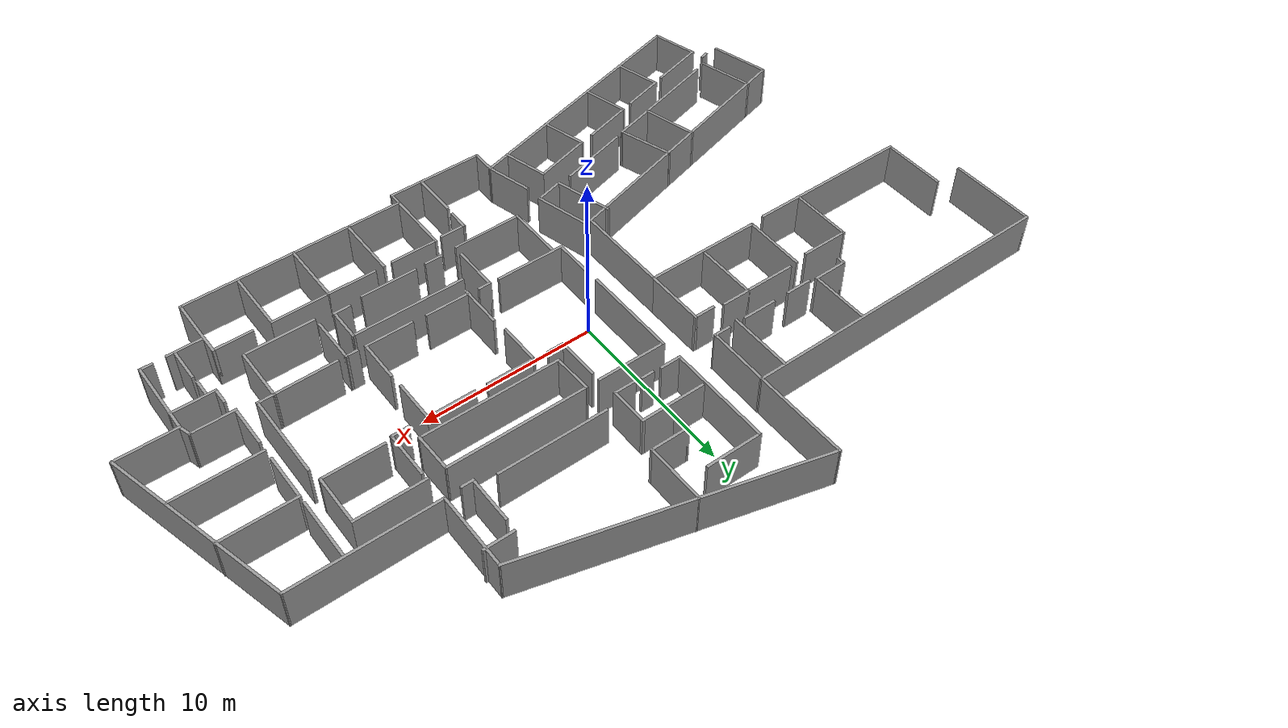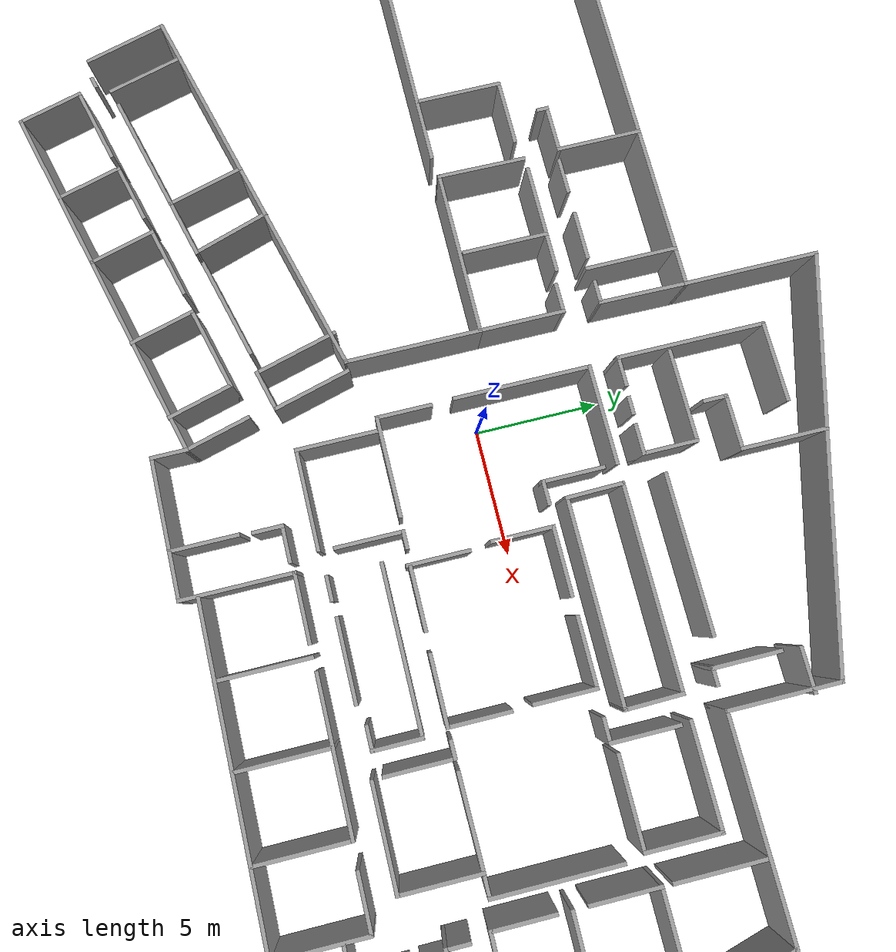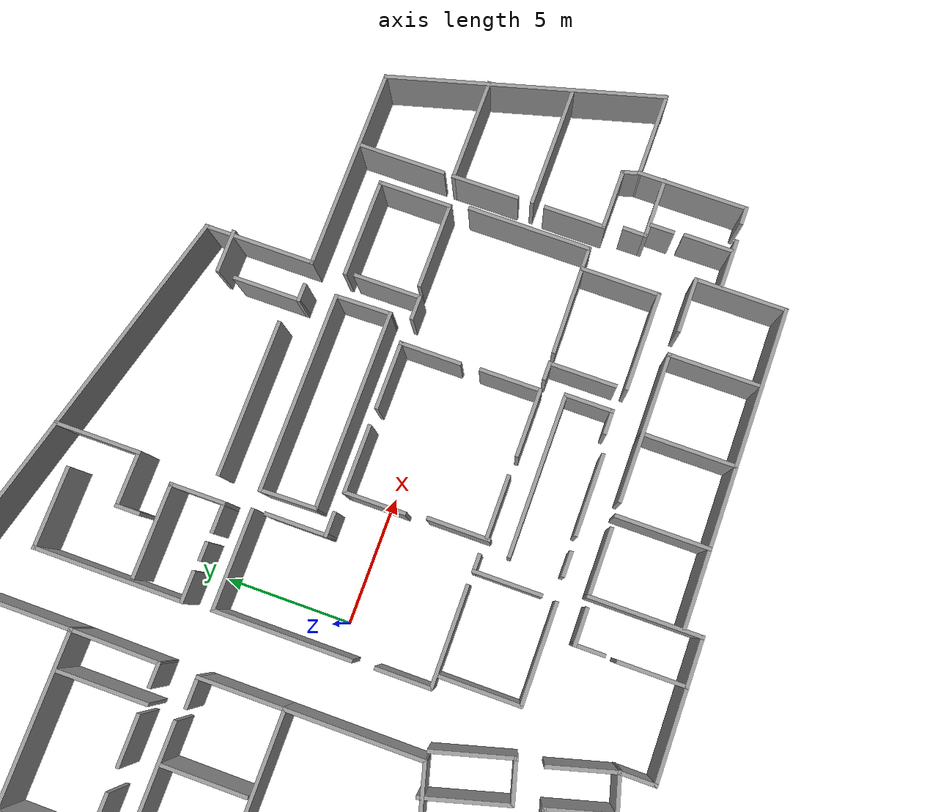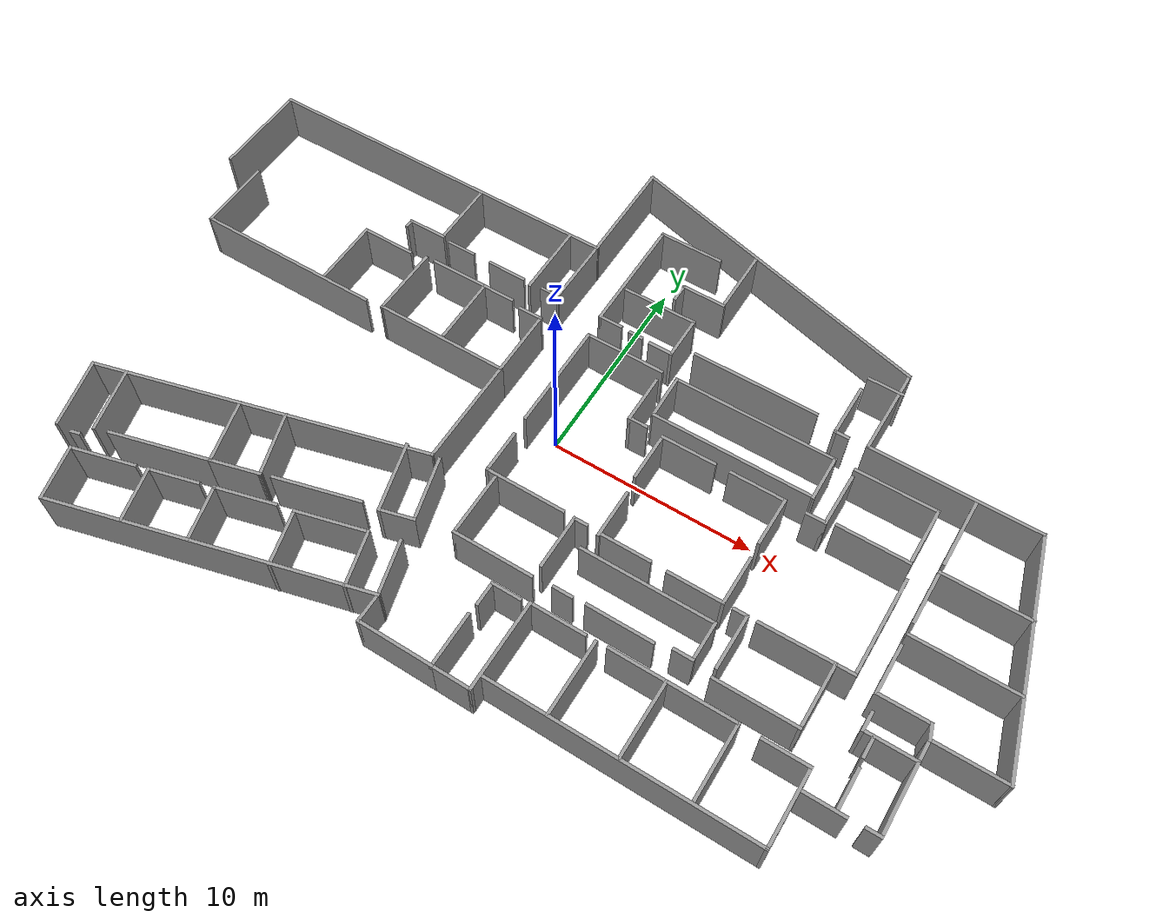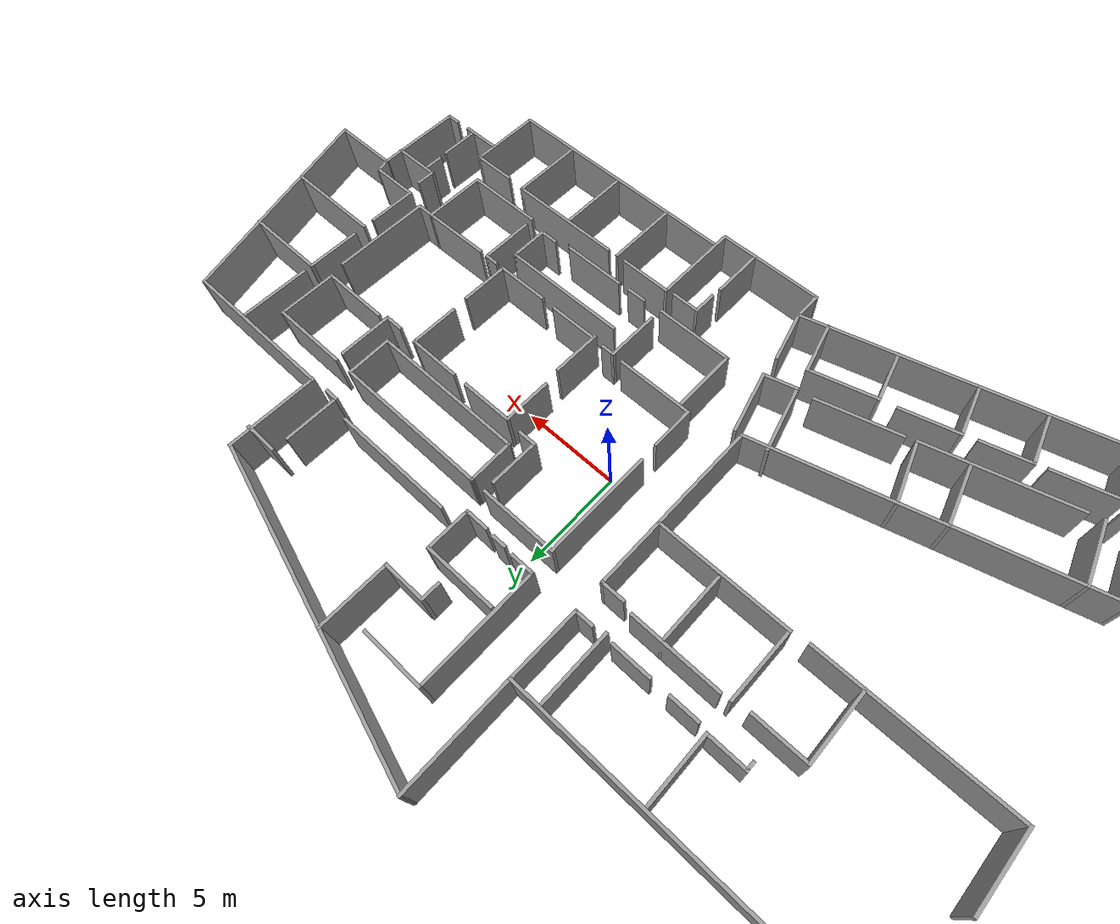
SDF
<?xml version='1.0'?>
<sdf version='1.7'>
  <model name='DohertyGazeboModel'>
    <pose>0.626728 -0.28149 0 0 -0 0</pose>
    <link name='Wall_0'>
      <collision name='Wall_0_Collision'>
        <geometry>
          <box>
            <size>5 0.15 2.5</size>
          </box>
        </geometry>
        <pose>0 0 1.25 0 -0 0</pose>
      </collision>
      <visual name='Wall_0_Visual'>
        <pose>0 0 1.25 0 -0 0</pose>
        <geometry>
          <box>
            <size>5 0.15 2.5</size>
          </box>
        </geometry>
        <material>
          <script>
            <uri>file://media/materials/scripts/gazebo.material</uri>
            <name>Gazebo/Grey</name>
          </script>
          <ambient>1 1 1 1</ambient>
        </material>
        <meta>
          <layer>0</layer>
        </meta>
      </visual>
      <pose>-22.6913 7.0385 0 0 -0 1.5708</pose>
    </link>
    <link name='Wall_1'>
      <collision name='Wall_1_Collision'>
        <geometry>
          <box>
            <size>18.75 0.15 2.5</size>
          </box>
        </geometry>
        <pose>0 0 1.25 0 -0 0</pose>
      </collision>
      <visual name='Wall_1_Visual'>
        <pose>0 0 1.25 0 -0 0</pose>
        <geometry>
          <box>
            <size>18.75 0.15 2.5</size>
          </box>
        </geometry>
        <material>
          <script>
            <uri>file://media/materials/scripts/gazebo.material</uri>
            <name>Gazebo/Grey</name>
          </script>
          <ambient>1 1 1 1</ambient>
        </material>
        <meta>
          <layer>0</layer>
        </meta>
      </visual>
      <pose>-13.3913 9.4635 0 0 -0 0</pose>
    </link>
    <link name='Wall_10'>
      <collision name='Wall_10_Collision'>
        <geometry>
          <box>
            <size>3.75 0.15 2.5</size>
          </box>
        </geometry>
        <pose>0 0 1.25 0 -0 0</pose>
      </collision>
      <visual name='Wall_10_Visual'>
        <pose>0 0 1.25 0 -0 0</pose>
        <geometry>
          <box>
            <size>3.75 0.15 2.5</size>
          </box>
        </geometry>
        <material>
          <script>
            <uri>file://media/materials/scripts/gazebo.material</uri>
            <name>Gazebo/Grey</name>
          </script>
          <ambient>1 1 1 1</ambient>
        </material>
        <meta>
          <layer>0</layer>
        </meta>
      </visual>
      <pose>-20.9645 2.83778 0 0 -0 -1.5708</pose>
    </link>
    <link name='Wall_100'>
      <collision name='Wall_100_Collision'>
        <geometry>
          <box>
            <size>4.5 0.15 2.5</size>
          </box>
        </geometry>
        <pose>0 0 1.25 0 -0 0</pose>
      </collision>
      <visual name='Wall_100_Visual'>
        <pose>0 0 1.25 0 -0 0</pose>
        <geometry>
          <box>
            <size>4.5 0.15 2.5</size>
          </box>
        </geometry>
        <material>
          <script>
            <uri>file://media/materials/scripts/gazebo.material</uri>
            <name>Gazebo/Grey</name>
          </script>
          <ambient>1 1 1 1</ambient>
        </material>
        <meta>
          <layer>0</layer>
        </meta>
      </visual>
      <pose>3.28044 -10.0156 0 0 -0 1.5708</pose>
    </link>
    <link name='Wall_102'>
      <collision name='Wall_102_Collision'>
        <geometry>
          <box>
            <size>12.75 0.15 2.5</size>
          </box>
        </geometry>
        <pose>0 0 1.25 0 -0 0</pose>
      </collision>
      <visual name='Wall_102_Visual'>
        <pose>0 0 1.25 0 -0 0</pose>
        <geometry>
          <box>
            <size>12.75 0.15 2.5</size>
          </box>
        </geometry>
        <material>
          <script>
            <uri>file://media/materials/scripts/gazebo.material</uri>
            <name>Gazebo/Grey</name>
          </script>
          <ambient>1 1 1 1</ambient>
        </material>
        <meta>
          <layer>0</layer>
        </meta>
      </visual>
      <pose>9.66138 -11.4757 0 0 -0 0</pose>
    </link>
    <link name='Wall_103'>
      <collision name='Wall_103_Collision'>
        <geometry>
          <box>
            <size>3.75 0.15 2.5</size>
          </box>
        </geometry>
        <pose>0 0 1.25 0 -0 0</pose>
      </collision>
      <visual name='Wall_103_Visual'>
        <pose>0 0 1.25 0 -0 0</pose>
        <geometry>
          <box>
            <size>3.75 0.15 2.5</size>
          </box>
        </geometry>
        <material>
          <script>
            <uri>file://media/materials/scripts/gazebo.material</uri>
            <name>Gazebo/Grey</name>
          </script>
          <ambient>1 1 1 1</ambient>
        </material>
        <meta>
          <layer>0</layer>
        </meta>
      </visual>
      <pose>15.9614 -9.67571 0 0 -0 1.5708</pose>
    </link>
    <link name='Wall_104'>
      <collision name='Wall_104_Collision'>
        <geometry>
          <box>
            <size>2.25 0.15 2.5</size>
          </box>
        </geometry>
        <pose>0 0 1.25 0 -0 0</pose>
      </collision>
      <visual name='Wall_104_Visual'>
        <pose>0 0 1.25 0 -0 0</pose>
        <geometry>
          <box>
            <size>2.25 0.15 2.5</size>
          </box>
        </geometry>
        <material>
          <script>
            <uri>file://media/materials/scripts/gazebo.material</uri>
            <name>Gazebo/Grey</name>
          </script>
          <ambient>1 1 1 1</ambient>
        </material>
        <meta>
          <layer>0</layer>
        </meta>
      </visual>
      <pose>14.9114 -7.87571 0 0 -0 3.14159</pose>
    </link>
    <link name='Wall_106'>
      <collision name='Wall_106_Collision'>
        <geometry>
          <box>
            <size>2.75 0.15 2.5</size>
          </box>
        </geometry>
        <pose>0 0 1.25 0 -0 0</pose>
      </collision>
      <visual name='Wall_106_Visual'>
        <pose>0 0 1.25 0 -0 0</pose>
        <geometry>
          <box>
            <size>2.75 0.15 2.5</size>
          </box>
        </geometry>
        <material>
          <script>
            <uri>file://media/materials/scripts/gazebo.material</uri>
            <name>Gazebo/Grey</name>
          </script>
          <ambient>1 1 1 1</ambient>
        </material>
        <meta>
          <layer>0</layer>
        </meta>
      </visual>
      <pose>4.58045 -7.84063 0 0 -0 0</pose>
    </link>
    <link name='Wall_108'>
      <collision name='Wall_108_Collision'>
        <geometry>
          <box>
            <size>3.75 0.15 2.5</size>
          </box>
        </geometry>
        <pose>0 0 1.25 0 -0 0</pose>
      </collision>
      <visual name='Wall_108_Visual'>
        <pose>0 0 1.25 0 -0 0</pose>
        <geometry>
          <box>
            <size>3.75 0.15 2.5</size>
          </box>
        </geometry>
        <material>
          <script>
            <uri>file://media/materials/scripts/gazebo.material</uri>
            <name>Gazebo/Grey</name>
          </script>
          <ambient>1 1 1 1</ambient>
        </material>
        <meta>
          <layer>0</layer>
        </meta>
      </visual>
      <pose>6.39368 -9.66583 0 0 -0 -1.5708</pose>
    </link>
    <link name='Wall_11'>
      <collision name='Wall_11_Collision'>
        <geometry>
          <box>
            <size>9.5 0.15 2.5</size>
          </box>
        </geometry>
        <pose>0 0 1.25 0 -0 0</pose>
      </collision>
      <visual name='Wall_11_Visual'>
        <pose>0 0 1.25 0 -0 0</pose>
        <geometry>
          <box>
            <size>9.5 0.15 2.5</size>
          </box>
        </geometry>
        <material>
          <script>
            <uri>file://media/materials/scripts/gazebo.material</uri>
            <name>Gazebo/Grey</name>
          </script>
          <ambient>1 1 1 1</ambient>
        </material>
        <meta>
          <layer>0</layer>
        </meta>
      </visual>
      <pose>-16.2895 1.03778 0 0 -0 0</pose>
    </link>
    <link name='Wall_110'>
      <collision name='Wall_110_Collision'>
        <geometry>
          <box>
            <size>6 0.15 2.5</size>
          </box>
        </geometry>
        <pose>0 0 1.25 0 -0 0</pose>
      </collision>
      <visual name='Wall_110_Visual'>
        <pose>0 0 1.25 0 -0 0</pose>
        <geometry>
          <box>
            <size>6 0.15 2.5</size>
          </box>
        </geometry>
        <material>
          <script>
            <uri>file://media/materials/scripts/gazebo.material</uri>
            <name>Gazebo/Grey</name>
          </script>
          <ambient>1 1 1 1</ambient>
        </material>
        <meta>
          <layer>0</layer>
        </meta>
      </visual>
      <pose>9.89626 -7.8177 0 0 -0 0</pose>
    </link>
    <link name='Wall_112'>
      <collision name='Wall_112_Collision'>
        <geometry>
          <box>
            <size>3.75 0.15 2.5</size>
          </box>
        </geometry>
        <pose>0 0 1.25 0 -0 0</pose>
      </collision>
      <visual name='Wall_112_Visual'>
        <pose>0 0 1.25 0 -0 0</pose>
        <geometry>
          <box>
            <size>3.75 0.15 2.5</size>
          </box>
        </geometry>
        <material>
          <script>
            <uri>file://media/materials/scripts/gazebo.material</uri>
            <name>Gazebo/Grey</name>
          </script>
          <ambient>1 1 1 1</ambient>
        </material>
        <meta>
          <layer>0</layer>
        </meta>
      </visual>
      <pose>9.61851 -9.6177 0 0 -0 -1.5708</pose>
    </link>
    <link name='Wall_114'>
      <collision name='Wall_114_Collision'>
        <geometry>
          <box>
            <size>3.75 0.15 2.5</size>
          </box>
        </geometry>
        <pose>0 0 1.25 0 -0 0</pose>
      </collision>
      <visual name='Wall_114_Visual'>
        <pose>0 0 1.25 0 -0 0</pose>
        <geometry>
          <box>
            <size>3.75 0.15 2.5</size>
          </box>
        </geometry>
        <material>
          <script>
            <uri>file://media/materials/scripts/gazebo.material</uri>
            <name>Gazebo/Grey</name>
          </script>
          <ambient>1 1 1 1</ambient>
        </material>
        <meta>
          <layer>0</layer>
        </meta>
      </visual>
      <pose>12.8213 -9.6177 0 0 -0 -1.5708</pose>
    </link>
    <link name='Wall_116'>
      <collision name='Wall_116_Collision'>
        <geometry>
          <box>
            <size>1.25 0.15 2.5</size>
          </box>
        </geometry>
        <pose>0 0 1.25 0 -0 0</pose>
      </collision>
      <visual name='Wall_116_Visual'>
        <pose>0 0 1.25 0 -0 0</pose>
        <geometry>
          <box>
            <size>1.25 0.15 2.5</size>
          </box>
        </geometry>
        <material>
          <script>
            <uri>file://media/materials/scripts/gazebo.material</uri>
            <name>Gazebo/Grey</name>
          </script>
          <ambient>1 1 1 1</ambient>
        </material>
        <meta>
          <layer>0</layer>
        </meta>
      </visual>
      <pose>1.48424 -8.47099 0 0 -0 1.5708</pose>
    </link>
    <link name='Wall_117'>
      <collision name='Wall_117_Collision'>
        <geometry>
          <box>
            <size>1.5 0.15 2.5</size>
          </box>
        </geometry>
        <pose>0 0 1.25 0 -0 0</pose>
      </collision>
      <visual name='Wall_117_Visual'>
        <pose>0 0 1.25 0 -0 0</pose>
        <geometry>
          <box>
            <size>1.5 0.15 2.5</size>
          </box>
        </geometry>
        <material>
          <script>
            <uri>file://media/materials/scripts/gazebo.material</uri>
            <name>Gazebo/Grey</name>
          </script>
          <ambient>1 1 1 1</ambient>
        </material>
        <meta>
          <layer>0</layer>
        </meta>
      </visual>
      <pose>2.15924 -7.92099 0 0 -0 0</pose>
    </link>
    <link name='Wall_119'>
      <collision name='Wall_119_Collision'>
        <geometry>
          <box>
            <size>0.75 0.15 2.5</size>
          </box>
        </geometry>
        <pose>0 0 1.25 0 -0 0</pose>
      </collision>
      <visual name='Wall_119_Visual'>
        <pose>0 0 1.25 0 -0 0</pose>
        <geometry>
          <box>
            <size>0.75 0.15 2.5</size>
          </box>
        </geometry>
        <material>
          <script>
            <uri>file://media/materials/scripts/gazebo.material</uri>
            <name>Gazebo/Grey</name>
          </script>
          <ambient>1 1 1 1</ambient>
        </material>
        <meta>
          <layer>0</layer>
        </meta>
      </visual>
      <pose>19.0245 -8.83996 0 0 -0 3.14159</pose>
    </link>
    <link name='Wall_121'>
      <collision name='Wall_121_Collision'>
        <geometry>
          <box>
            <size>2 0.15 2.5</size>
          </box>
        </geometry>
        <pose>0 0 1.25 0 -0 0</pose>
      </collision>
      <visual name='Wall_121_Visual'>
        <pose>0 0 1.25 0 -0 0</pose>
        <geometry>
          <box>
            <size>2 0.15 2.5</size>
          </box>
        </geometry>
        <material>
          <script>
            <uri>file://media/materials/scripts/gazebo.material</uri>
            <name>Gazebo/Grey</name>
          </script>
          <ambient>1 1 1 1</ambient>
        </material>
        <meta>
          <layer>0</layer>
        </meta>
      </visual>
      <pose>16.9932 -8.8766 0 0 -0 0</pose>
    </link>
    <link name='Wall_125'>
      <collision name='Wall_125_Collision'>
        <geometry>
          <box>
            <size>1 0.15 2.5</size>
          </box>
        </geometry>
        <pose>0 0 1.25 0 -0 0</pose>
      </collision>
      <visual name='Wall_125_Visual'>
        <pose>0 0 1.25 0 -0 0</pose>
        <geometry>
          <box>
            <size>1 0.15 2.5</size>
          </box>
        </geometry>
        <material>
          <script>
            <uri>file://media/materials/scripts/gazebo.material</uri>
            <name>Gazebo/Grey</name>
          </script>
          <ambient>1 1 1 1</ambient>
        </material>
        <meta>
          <layer>0</layer>
        </meta>
      </visual>
      <pose>17.464 -6.02864 0 0 -0 -1.5708</pose>
    </link>
    <link name='Wall_127'>
      <collision name='Wall_127_Collision'>
        <geometry>
          <box>
            <size>2 0.15 2.5</size>
          </box>
        </geometry>
        <pose>0 0 1.25 0 -0 0</pose>
      </collision>
      <visual name='Wall_127_Visual'>
        <pose>0 0 1.25 0 -0 0</pose>
        <geometry>
          <box>
            <size>2 0.15 2.5</size>
          </box>
        </geometry>
        <material>
          <script>
            <uri>file://media/materials/scripts/gazebo.material</uri>
            <name>Gazebo/Grey</name>
          </script>
          <ambient>1 1 1 1</ambient>
        </material>
        <meta>
          <layer>0</layer>
        </meta>
      </visual>
      <pose>17.5121 -7.87633 0 0 -0 -1.5708</pose>
    </link>
    <link name='Wall_129'>
      <collision name='Wall_129_Collision'>
        <geometry>
          <box>
            <size>3.5 0.15 2.5</size>
          </box>
        </geometry>
        <pose>0 0 1.25 0 -0 0</pose>
      </collision>
      <visual name='Wall_129_Visual'>
        <pose>0 0 1.25 0 -0 0</pose>
        <geometry>
          <box>
            <size>3.5 0.15 2.5</size>
          </box>
        </geometry>
        <material>
          <script>
            <uri>file://media/materials/scripts/gazebo.material</uri>
            <name>Gazebo/Grey</name>
          </script>
          <ambient>1 1 1 1</ambient>
        </material>
        <meta>
          <layer>0</layer>
        </meta>
      </visual>
      <pose>2.70333 11.3169 0 0 -0 -1.5708</pose>
    </link>
    <link name='Wall_13'>
      <collision name='Wall_13_Collision'>
        <geometry>
          <box>
            <size>6.75 0.15 2.5</size>
          </box>
        </geometry>
        <pose>0 0 1.25 0 -0 0</pose>
      </collision>
      <visual name='Wall_13_Visual'>
        <pose>0 0 1.25 0 -0 0</pose>
        <geometry>
          <box>
            <size>6.75 0.15 2.5</size>
          </box>
        </geometry>
        <material>
          <script>
            <uri>file://media/materials/scripts/gazebo.material</uri>
            <name>Gazebo/Grey</name>
          </script>
          <ambient>1 1 1 1</ambient>
        </material>
        <meta>
          <layer>0</layer>
        </meta>
      </visual>
      <pose>-7.41613 1.1368 0 0 -0 0</pose>
    </link>
    <link name='Wall_130'>
      <collision name='Wall_130_Collision'>
        <geometry>
          <box>
            <size>2.25 0.15 2.5</size>
          </box>
        </geometry>
        <pose>0 0 1.25 0 -0 0</pose>
      </collision>
      <visual name='Wall_130_Visual'>
        <pose>0 0 1.25 0 -0 0</pose>
        <geometry>
          <box>
            <size>2.25 0.15 2.5</size>
          </box>
        </geometry>
        <material>
          <script>
            <uri>file://media/materials/scripts/gazebo.material</uri>
            <name>Gazebo/Grey</name>
          </script>
          <ambient>1 1 1 1</ambient>
        </material>
        <meta>
          <layer>0</layer>
        </meta>
      </visual>
      <pose>1.65333 9.64189 0 0 -0 3.14159</pose>
    </link>
    <link name='Wall_131'>
      <collision name='Wall_131_Collision'>
        <geometry>
          <box>
            <size>1 0.15 2.5</size>
          </box>
        </geometry>
        <pose>0 0 1.25 0 -0 0</pose>
      </collision>
      <visual name='Wall_131_Visual'>
        <pose>0 0 1.25 0 -0 0</pose>
        <geometry>
          <box>
            <size>1 0.15 2.5</size>
          </box>
        </geometry>
        <material>
          <script>
            <uri>file://media/materials/scripts/gazebo.material</uri>
            <name>Gazebo/Grey</name>
          </script>
          <ambient>1 1 1 1</ambient>
        </material>
        <meta>
          <layer>0</layer>
        </meta>
      </visual>
      <pose>0.603331 9.21689 0 0 -0 -1.5708</pose>
    </link>
    <link name='Wall_133'>
      <collision name='Wall_133_Collision'>
        <geometry>
          <box>
            <size>1.75 0.15 2.5</size>
          </box>
        </geometry>
        <pose>0 0 1.25 0 -0 0</pose>
      </collision>
      <visual name='Wall_133_Visual'>
        <pose>0 0 1.25 0 -0 0</pose>
        <geometry>
          <box>
            <size>1.75 0.15 2.5</size>
          </box>
        </geometry>
        <material>
          <script>
            <uri>file://media/materials/scripts/gazebo.material</uri>
            <name>Gazebo/Grey</name>
          </script>
          <ambient>1 1 1 1</ambient>
        </material>
        <meta>
          <layer>0</layer>
        </meta>
      </visual>
      <pose>11.0274 9.51804 0 0 -0 3.14159</pose>
    </link>
    <link name='Wall_139'>
      <collision name='Wall_139_Collision'>
        <geometry>
          <box>
            <size>0.75 0.15 2.5</size>
          </box>
        </geometry>
        <pose>0 0 1.25 0 -0 0</pose>
      </collision>
      <visual name='Wall_139_Visual'>
        <pose>0 0 1.25 0 -0 0</pose>
        <geometry>
          <box>
            <size>0.75 0.15 2.5</size>
          </box>
        </geometry>
        <material>
          <script>
            <uri>file://media/materials/scripts/gazebo.material</uri>
            <name>Gazebo/Grey</name>
          </script>
          <ambient>1 1 1 1</ambient>
        </material>
        <meta>
          <layer>0</layer>
        </meta>
      </visual>
      <pose>10.4533 6.16974 0 0 -0 0</pose>
    </link>
    <link name='Wall_14'>
      <collision name='Wall_14_Collision'>
        <geometry>
          <box>
            <size>5.5 0.15 2.5</size>
          </box>
        </geometry>
        <pose>0 0 1.25 0 -0 0</pose>
      </collision>
      <visual name='Wall_14_Visual'>
        <pose>0 0 1.25 0 -0 0</pose>
        <geometry>
          <box>
            <size>5.5 0.15 2.5</size>
          </box>
        </geometry>
        <material>
          <script>
            <uri>file://media/materials/scripts/gazebo.material</uri>
            <name>Gazebo/Grey</name>
          </script>
          <ambient>1 1 1 1</ambient>
        </material>
        <meta>
          <layer>0</layer>
        </meta>
      </visual>
      <pose>-4.11613 -1.5382 0 0 -0 -1.5708</pose>
    </link>
    <link name='Wall_141'>
      <collision name='Wall_141_Collision'>
        <geometry>
          <box>
            <size>2.75 0.15 2.5</size>
          </box>
        </geometry>
        <pose>0 0 1.25 0 -0 0</pose>
      </collision>
      <visual name='Wall_141_Visual'>
        <pose>0 0 1.25 0 -0 0</pose>
        <geometry>
          <box>
            <size>2.75 0.15 2.5</size>
          </box>
        </geometry>
        <material>
          <script>
            <uri>file://media/materials/scripts/gazebo.material</uri>
            <name>Gazebo/Grey</name>
          </script>
          <ambient>1 1 1 1</ambient>
        </material>
        <meta>
          <layer>0</layer>
        </meta>
      </visual>
      <pose>10.1533 7.46974 0 0 -0 1.5708</pose>
    </link>
    <link name='Wall_143'>
      <collision name='Wall_143_Collision'>
        <geometry>
          <box>
            <size>3.25 0.15 2.5</size>
          </box>
        </geometry>
        <pose>0 0 1.25 0 -0 0</pose>
      </collision>
      <visual name='Wall_143_Visual'>
        <pose>0 0 1.25 0 -0 0</pose>
        <geometry>
          <box>
            <size>3.25 0.15 2.5</size>
          </box>
        </geometry>
        <material>
          <script>
            <uri>file://media/materials/scripts/gazebo.material</uri>
            <name>Gazebo/Grey</name>
          </script>
          <ambient>1 1 1 1</ambient>
        </material>
        <meta>
          <layer>0</layer>
        </meta>
      </visual>
      <pose>-0.269694 11.9037 0 0 -0 3.14159</pose>
    </link>
    <link name='Wall_144'>
      <collision name='Wall_144_Collision'>
        <geometry>
          <box>
            <size>6 0.15 2.5</size>
          </box>
        </geometry>
        <pose>0 0 1.25 0 -0 0</pose>
      </collision>
      <visual name='Wall_144_Visual'>
        <pose>0 0 1.25 0 -0 0</pose>
        <geometry>
          <box>
            <size>6 0.15 2.5</size>
          </box>
        </geometry>
        <material>
          <script>
            <uri>file://media/materials/scripts/gazebo.material</uri>
            <name>Gazebo/Grey</name>
          </script>
          <ambient>1 1 1 1</ambient>
        </material>
        <meta>
          <layer>0</layer>
        </meta>
      </visual>
      <pose>-1.81969 8.9787 0 0 -0 -1.5708</pose>
    </link>
    <link name='Wall_145'>
      <collision name='Wall_145_Collision'>
        <geometry>
          <box>
            <size>1.25 0.15 2.5</size>
          </box>
        </geometry>
        <pose>0 0 1.25 0 -0 0</pose>
      </collision>
      <visual name='Wall_145_Visual'>
        <pose>0 0 1.25 0 -0 0</pose>
        <geometry>
          <box>
            <size>1.25 0.15 2.5</size>
          </box>
        </geometry>
        <material>
          <script>
            <uri>file://media/materials/scripts/gazebo.material</uri>
            <name>Gazebo/Grey</name>
          </script>
          <ambient>1 1 1 1</ambient>
        </material>
        <meta>
          <layer>0</layer>
        </meta>
      </visual>
      <pose>-1.26969 6.0537 0 0 -0 0</pose>
    </link>
    <link name='Wall_147'>
      <collision name='Wall_147_Collision'>
        <geometry>
          <box>
            <size>0.75 0.15 2.5</size>
          </box>
        </geometry>
        <pose>0 0 1.25 0 -0 0</pose>
      </collision>
      <visual name='Wall_147_Visual'>
        <pose>0 0 1.25 0 -0 0</pose>
        <geometry>
          <box>
            <size>0.75 0.15 2.5</size>
          </box>
        </geometry>
        <material>
          <script>
            <uri>file://media/materials/scripts/gazebo.material</uri>
            <name>Gazebo/Grey</name>
          </script>
          <ambient>1 1 1 1</ambient>
        </material>
        <meta>
          <layer>0</layer>
        </meta>
      </visual>
      <pose>0.115427 6.00233 0 0 -0 0</pose>
    </link>
    <link name='Wall_149'>
      <collision name='Wall_149_Collision'>
        <geometry>
          <box>
            <size>1.25 0.15 2.5</size>
          </box>
        </geometry>
        <pose>0 0 1.25 0 -0 0</pose>
      </collision>
      <visual name='Wall_149_Visual'>
        <pose>0 0 1.25 0 -0 0</pose>
        <geometry>
          <box>
            <size>1.25 0.15 2.5</size>
          </box>
        </geometry>
        <material>
          <script>
            <uri>file://media/materials/scripts/gazebo.material</uri>
            <name>Gazebo/Grey</name>
          </script>
          <ambient>1 1 1 1</ambient>
        </material>
        <meta>
          <layer>0</layer>
        </meta>
      </visual>
      <pose>1.45362 5.96048 0 0 -0 0</pose>
    </link>
    <link name='Wall_15'>
      <collision name='Wall_15_Collision'>
        <geometry>
          <box>
            <size>16.5 0.15 2.5</size>
          </box>
        </geometry>
        <pose>0 0 1.25 0 -0 0</pose>
      </collision>
      <visual name='Wall_15_Visual'>
        <pose>0 0 1.25 0 -0 0</pose>
        <geometry>
          <box>
            <size>16.5 0.15 2.5</size>
          </box>
        </geometry>
        <material>
          <script>
            <uri>file://media/materials/scripts/gazebo.material</uri>
            <name>Gazebo/Grey</name>
          </script>
          <ambient>1 1 1 1</ambient>
        </material>
        <meta>
          <layer>0</layer>
        </meta>
      </visual>
      <pose>-12.0126 -6.32905 0 0 -0 -2.87979</pose>
    </link>
    <link name='Wall_150'>
      <collision name='Wall_150_Collision'>
        <geometry>
          <box>
            <size>2.25 0.15 2.5</size>
          </box>
        </geometry>
        <pose>0 0 1.25 0 -0 0</pose>
      </collision>
      <visual name='Wall_150_Visual'>
        <pose>0 0 1.25 0 -0 0</pose>
        <geometry>
          <box>
            <size>2.25 0.15 2.5</size>
          </box>
        </geometry>
        <material>
          <script>
            <uri>file://media/materials/scripts/gazebo.material</uri>
            <name>Gazebo/Grey</name>
          </script>
          <ambient>1 1 1 1</ambient>
        </material>
        <meta>
          <layer>0</layer>
        </meta>
      </visual>
      <pose>2.00362 7.01048 0 0 -0 1.5708</pose>
    </link>
    <link name='Wall_151'>
      <collision name='Wall_151_Collision'>
        <geometry>
          <box>
            <size>3.75 0.15 2.5</size>
          </box>
        </geometry>
        <pose>0 0 1.25 0 -0 0</pose>
      </collision>
      <visual name='Wall_151_Visual'>
        <pose>0 0 1.25 0 -0 0</pose>
        <geometry>
          <box>
            <size>3.75 0.15 2.5</size>
          </box>
        </geometry>
        <material>
          <script>
            <uri>file://media/materials/scripts/gazebo.material</uri>
            <name>Gazebo/Grey</name>
          </script>
          <ambient>1 1 1 1</ambient>
        </material>
        <meta>
          <layer>0</layer>
        </meta>
      </visual>
      <pose>0.203623 8.06048 0 0 -0 3.14159</pose>
    </link>
    <link name='Wall_153'>
      <collision name='Wall_153_Collision'>
        <geometry>
          <box>
            <size>6.25 0.15 2.5</size>
          </box>
        </geometry>
        <pose>0 0 1.25 0 -0 0</pose>
      </collision>
      <visual name='Wall_153_Visual'>
        <pose>0 0 1.25 0 -0 0</pose>
        <geometry>
          <box>
            <size>6.25 0.15 2.5</size>
          </box>
        </geometry>
        <material>
          <script>
            <uri>file://media/materials/scripts/gazebo.material</uri>
            <name>Gazebo/Grey</name>
          </script>
          <ambient>1 1 1 1</ambient>
        </material>
        <meta>
          <layer>0</layer>
        </meta>
      </visual>
      <pose>6.00445 6.54643 0 0 -0 0</pose>
    </link>
    <link name='Wall_155'>
      <collision name='Wall_155_Collision'>
        <geometry>
          <box>
            <size>4 0.15 2.5</size>
          </box>
        </geometry>
        <pose>0 0 1.25 0 -0 0</pose>
      </collision>
      <visual name='Wall_155_Visual'>
        <pose>0 0 1.25 0 -0 0</pose>
        <geometry>
          <box>
            <size>4 0.15 2.5</size>
          </box>
        </geometry>
        <material>
          <script>
            <uri>file://media/materials/scripts/gazebo.material</uri>
            <name>Gazebo/Grey</name>
          </script>
          <ambient>1 1 1 1</ambient>
        </material>
        <meta>
          <layer>0</layer>
        </meta>
      </visual>
      <pose>0.19238 4.87228 0 0 -0 3.14159</pose>
    </link>
    <link name='Wall_156'>
      <collision name='Wall_156_Collision'>
        <geometry>
          <box>
            <size>5.5 0.15 2.5</size>
          </box>
        </geometry>
        <pose>0 0 1.25 0 -0 0</pose>
      </collision>
      <visual name='Wall_156_Visual'>
        <pose>0 0 1.25 0 -0 0</pose>
        <geometry>
          <box>
            <size>5.5 0.15 2.5</size>
          </box>
        </geometry>
        <material>
          <script>
            <uri>file://media/materials/scripts/gazebo.material</uri>
            <name>Gazebo/Grey</name>
          </script>
          <ambient>1 1 1 1</ambient>
        </material>
        <meta>
          <layer>0</layer>
        </meta>
      </visual>
      <pose>-1.73262 2.19728 0 0 -0 -1.5708</pose>
    </link>
    <link name='Wall_158'>
      <collision name='Wall_158_Collision'>
        <geometry>
          <box>
            <size>2.25 0.15 2.5</size>
          </box>
        </geometry>
        <pose>0 0 1.25 0 -0 0</pose>
      </collision>
      <visual name='Wall_158_Visual'>
        <pose>0 0 1.25 0 -0 0</pose>
        <geometry>
          <box>
            <size>2.25 0.15 2.5</size>
          </box>
        </geometry>
        <material>
          <script>
            <uri>file://media/materials/scripts/gazebo.material</uri>
            <name>Gazebo/Grey</name>
          </script>
          <ambient>1 1 1 1</ambient>
        </material>
        <meta>
          <layer>0</layer>
        </meta>
      </visual>
      <pose>-1.69131 -2.49763 0 0 -0 -1.5708</pose>
    </link>
    <link name='Wall_159'>
      <collision name='Wall_159_Collision'>
        <geometry>
          <box>
            <size>4 0.15 2.5</size>
          </box>
        </geometry>
        <pose>0 0 1.25 0 -0 0</pose>
      </collision>
      <visual name='Wall_159_Visual'>
        <pose>0 0 1.25 0 -0 0</pose>
        <geometry>
          <box>
            <size>4 0.15 2.5</size>
          </box>
        </geometry>
        <material>
          <script>
            <uri>file://media/materials/scripts/gazebo.material</uri>
            <name>Gazebo/Grey</name>
          </script>
          <ambient>1 1 1 1</ambient>
        </material>
        <meta>
          <layer>0</layer>
        </meta>
      </visual>
      <pose>0.233695 -3.54763 0 0 -0 0</pose>
    </link>
    <link name='Wall_16'>
      <collision name='Wall_16_Collision'>
        <geometry>
          <box>
            <size>3.5 0.15 2.5</size>
          </box>
        </geometry>
        <pose>0 0 1.25 0 -0 0</pose>
      </collision>
      <visual name='Wall_16_Visual'>
        <pose>0 0 1.25 0 -0 0</pose>
        <geometry>
          <box>
            <size>3.5 0.15 2.5</size>
          </box>
        </geometry>
        <material>
          <script>
            <uri>file://media/materials/scripts/gazebo.material</uri>
            <name>Gazebo/Grey</name>
          </script>
          <ambient>1 1 1 1</ambient>
        </material>
        <meta>
          <layer>0</layer>
        </meta>
      </visual>
      <pose>-19.4755 -10.0628 0 0 -0 -1.309</pose>
    </link>
    <link name='Wall_161'>
      <collision name='Wall_161_Collision'>
        <geometry>
          <box>
            <size>0.75 0.15 2.5</size>
          </box>
        </geometry>
        <pose>0 0 1.25 0 -0 0</pose>
      </collision>
      <visual name='Wall_161_Visual'>
        <pose>0 0 1.25 0 -0 0</pose>
        <geometry>
          <box>
            <size>0.75 0.15 2.5</size>
          </box>
        </geometry>
        <material>
          <script>
            <uri>file://media/materials/scripts/gazebo.material</uri>
            <name>Gazebo/Grey</name>
          </script>
          <ambient>1 1 1 1</ambient>
        </material>
        <meta>
          <layer>0</layer>
        </meta>
      </visual>
      <pose>3.04519 -3.58216 0 0 -0 0</pose>
    </link>
    <link name='Wall_163'>
      <collision name='Wall_163_Collision'>
        <geometry>
          <box>
            <size>3.25 0.15 2.5</size>
          </box>
        </geometry>
        <pose>0 0 1.25 0 -0 0</pose>
      </collision>
      <visual name='Wall_163_Visual'>
        <pose>0 0 1.25 0 -0 0</pose>
        <geometry>
          <box>
            <size>3.25 0.15 2.5</size>
          </box>
        </geometry>
        <material>
          <script>
            <uri>file://media/materials/scripts/gazebo.material</uri>
            <name>Gazebo/Grey</name>
          </script>
          <ambient>1 1 1 1</ambient>
        </material>
        <meta>
          <layer>0</layer>
        </meta>
      </visual>
      <pose>-1.18906 -5.25772 0 0 -0 -1.5708</pose>
    </link>
    <link name='Wall_164'>
      <collision name='Wall_164_Collision'>
        <geometry>
          <box>
            <size>4 0.15 2.5</size>
          </box>
        </geometry>
        <pose>0 0 1.25 0 -0 0</pose>
      </collision>
      <visual name='Wall_164_Visual'>
        <pose>0 0 1.25 0 -0 0</pose>
        <geometry>
          <box>
            <size>4 0.15 2.5</size>
          </box>
        </geometry>
        <material>
          <script>
            <uri>file://media/materials/scripts/gazebo.material</uri>
            <name>Gazebo/Grey</name>
          </script>
          <ambient>1 1 1 1</ambient>
        </material>
        <meta>
          <layer>0</layer>
        </meta>
      </visual>
      <pose>0.735939 -6.80772 0 0 -0 0</pose>
    </link>
    <link name='Wall_166'>
      <collision name='Wall_166_Collision'>
        <geometry>
          <box>
            <size>2.75 0.15 2.5</size>
          </box>
        </geometry>
        <pose>0 0 1.25 0 -0 0</pose>
      </collision>
      <visual name='Wall_166_Visual'>
        <pose>0 0 1.25 0 -0 0</pose>
        <geometry>
          <box>
            <size>2.75 0.15 2.5</size>
          </box>
        </geometry>
        <material>
          <script>
            <uri>file://media/materials/scripts/gazebo.material</uri>
            <name>Gazebo/Grey</name>
          </script>
          <ambient>1 1 1 1</ambient>
        </material>
        <meta>
          <layer>0</layer>
        </meta>
      </visual>
      <pose>2.74519 -4.88216 0 0 -0 -1.5708</pose>
    </link>
    <link name='Wall_168'>
      <collision name='Wall_168_Collision'>
        <geometry>
          <box>
            <size>2.5 0.15 2.5</size>
          </box>
        </geometry>
        <pose>0 0 1.25 0 -0 0</pose>
      </collision>
      <visual name='Wall_168_Visual'>
        <pose>0 0 1.25 0 -0 0</pose>
        <geometry>
          <box>
            <size>2.5 0.15 2.5</size>
          </box>
        </geometry>
        <material>
          <script>
            <uri>file://media/materials/scripts/gazebo.material</uri>
            <name>Gazebo/Grey</name>
          </script>
          <ambient>1 1 1 1</ambient>
        </material>
        <meta>
          <layer>0</layer>
        </meta>
      </visual>
      <pose>2.15923 3.15318 0 0 -0 -1.5708</pose>
    </link>
    <link name='Wall_169'>
      <collision name='Wall_169_Collision'>
        <geometry>
          <box>
            <size>1 0.15 2.5</size>
          </box>
        </geometry>
        <pose>0 0 1.25 0 -0 0</pose>
      </collision>
      <visual name='Wall_169_Visual'>
        <pose>0 0 1.25 0 -0 0</pose>
        <geometry>
          <box>
            <size>1 0.15 2.5</size>
          </box>
        </geometry>
        <material>
          <script>
            <uri>file://media/materials/scripts/gazebo.material</uri>
            <name>Gazebo/Grey</name>
          </script>
          <ambient>1 1 1 1</ambient>
        </material>
        <meta>
          <layer>0</layer>
        </meta>
      </visual>
      <pose>2.58423 1.97818 0 0 -0 0</pose>
    </link>
    <link name='Wall_171'>
      <collision name='Wall_171_Collision'>
        <geometry>
          <box>
            <size>2.75 0.15 2.5</size>
          </box>
        </geometry>
        <pose>0 0 1.25 0 -0 0</pose>
      </collision>
      <visual name='Wall_171_Visual'>
        <pose>0 0 1.25 0 -0 0</pose>
        <geometry>
          <box>
            <size>2.75 0.15 2.5</size>
          </box>
        </geometry>
        <material>
          <script>
            <uri>file://media/materials/scripts/gazebo.material</uri>
            <name>Gazebo/Grey</name>
          </script>
          <ambient>1 1 1 1</ambient>
        </material>
        <meta>
          <layer>0</layer>
        </meta>
      </visual>
      <pose>5.17523 1.90067 0 0 -0 0</pose>
    </link>
    <link name='Wall_173'>
      <collision name='Wall_173_Collision'>
        <geometry>
          <box>
            <size>2.75 0.15 2.5</size>
          </box>
        </geometry>
        <pose>0 0 1.25 0 -0 0</pose>
      </collision>
      <visual name='Wall_173_Visual'>
        <pose>0 0 1.25 0 -0 0</pose>
        <geometry>
          <box>
            <size>2.75 0.15 2.5</size>
          </box>
        </geometry>
        <material>
          <script>
            <uri>file://media/materials/scripts/gazebo.material</uri>
            <name>Gazebo/Grey</name>
          </script>
          <ambient>1 1 1 1</ambient>
        </material>
        <meta>
          <layer>0</layer>
        </meta>
      </visual>
      <pose>8.56538 1.90067 0 0 -0 0</pose>
    </link>
    <link name='Wall_174'>
      <collision name='Wall_174_Collision'>
        <geometry>
          <box>
            <size>2.5 0.15 2.5</size>
          </box>
        </geometry>
        <pose>0 0 1.25 0 -0 0</pose>
      </collision>
      <visual name='Wall_174_Visual'>
        <pose>0 0 1.25 0 -0 0</pose>
        <geometry>
          <box>
            <size>2.5 0.15 2.5</size>
          </box>
        </geometry>
        <material>
          <script>
            <uri>file://media/materials/scripts/gazebo.material</uri>
            <name>Gazebo/Grey</name>
          </script>
          <ambient>1 1 1 1</ambient>
        </material>
        <meta>
          <layer>0</layer>
        </meta>
      </visual>
      <pose>9.86538 0.72567 0 0 -0 -1.5708</pose>
    </link>
    <link name='Wall_178'>
      <collision name='Wall_178_Collision'>
        <geometry>
          <box>
            <size>2.5 0.15 2.5</size>
          </box>
        </geometry>
        <pose>0 0 1.25 0 -0 0</pose>
      </collision>
      <visual name='Wall_178_Visual'>
        <pose>0 0 1.25 0 -0 0</pose>
        <geometry>
          <box>
            <size>2.5 0.15 2.5</size>
          </box>
        </geometry>
        <material>
          <script>
            <uri>file://media/materials/scripts/gazebo.material</uri>
            <name>Gazebo/Grey</name>
          </script>
          <ambient>1 1 1 1</ambient>
        </material>
        <meta>
          <layer>0</layer>
        </meta>
      </visual>
      <pose>5.2595 -3.62402 0 0 -0 0</pose>
    </link>
    <link name='Wall_18'>
      <collision name='Wall_18_Collision'>
        <geometry>
          <box>
            <size>3.5 0.15 2.5</size>
          </box>
        </geometry>
        <pose>0 0 1.25 0 -0 0</pose>
      </collision>
      <visual name='Wall_18_Visual'>
        <pose>0 0 1.25 0 -0 0</pose>
        <geometry>
          <box>
            <size>3.5 0.15 2.5</size>
          </box>
        </geometry>
        <material>
          <script>
            <uri>file://media/materials/scripts/gazebo.material</uri>
            <name>Gazebo/Grey</name>
          </script>
          <ambient>1 1 1 1</ambient>
        </material>
        <meta>
          <layer>0</layer>
        </meta>
      </visual>
      <pose>-14.1116 2.80424 0 0 -0 1.5708</pose>
    </link>
    <link name='Wall_180'>
      <collision name='Wall_180_Collision'>
        <geometry>
          <box>
            <size>2.75 0.15 2.5</size>
          </box>
        </geometry>
        <pose>0 0 1.25 0 -0 0</pose>
      </collision>
      <visual name='Wall_180_Visual'>
        <pose>0 0 1.25 0 -0 0</pose>
        <geometry>
          <box>
            <size>2.75 0.15 2.5</size>
          </box>
        </geometry>
        <material>
          <script>
            <uri>file://media/materials/scripts/gazebo.material</uri>
            <name>Gazebo/Grey</name>
          </script>
          <ambient>1 1 1 1</ambient>
        </material>
        <meta>
          <layer>0</layer>
        </meta>
      </visual>
      <pose>8.60724 -3.66587 0 0 -0 0</pose>
    </link>
    <link name='Wall_182'>
      <collision name='Wall_182_Collision'>
        <geometry>
          <box>
            <size>2.5 0.15 2.5</size>
          </box>
        </geometry>
        <pose>0 0 1.25 0 -0 0</pose>
      </collision>
      <visual name='Wall_182_Visual'>
        <pose>0 0 1.25 0 -0 0</pose>
        <geometry>
          <box>
            <size>2.5 0.15 2.5</size>
          </box>
        </geometry>
        <material>
          <script>
            <uri>file://media/materials/scripts/gazebo.material</uri>
            <name>Gazebo/Grey</name>
          </script>
          <ambient>1 1 1 1</ambient>
        </material>
        <meta>
          <layer>0</layer>
        </meta>
      </visual>
      <pose>9.90724 -2.49087 0 0 -0 1.5708</pose>
    </link>
    <link name='Wall_184'>
      <collision name='Wall_184_Collision'>
        <geometry>
          <box>
            <size>2.5 0.15 2.5</size>
          </box>
        </geometry>
        <pose>0 0 1.25 0 -0 0</pose>
      </collision>
      <visual name='Wall_184_Visual'>
        <pose>0 0 1.25 0 -0 0</pose>
        <geometry>
          <box>
            <size>2.5 0.15 2.5</size>
          </box>
        </geometry>
        <material>
          <script>
            <uri>file://media/materials/scripts/gazebo.material</uri>
            <name>Gazebo/Grey</name>
          </script>
          <ambient>1 1 1 1</ambient>
        </material>
        <meta>
          <layer>0</layer>
        </meta>
      </visual>
      <pose>3.87523 0.72567 0 0 -0 -1.5708</pose>
    </link>
    <link name='Wall_186'>
      <collision name='Wall_186_Collision'>
        <geometry>
          <box>
            <size>2.5 0.15 2.5</size>
          </box>
        </geometry>
        <pose>0 0 1.25 0 -0 0</pose>
      </collision>
      <visual name='Wall_186_Visual'>
        <pose>0 0 1.25 0 -0 0</pose>
        <geometry>
          <box>
            <size>2.5 0.15 2.5</size>
          </box>
        </geometry>
        <material>
          <script>
            <uri>file://media/materials/scripts/gazebo.material</uri>
            <name>Gazebo/Grey</name>
          </script>
          <ambient>1 1 1 1</ambient>
        </material>
        <meta>
          <layer>0</layer>
        </meta>
      </visual>
      <pose>4.0008 -2.53892 0 0 -0 -1.5708</pose>
    </link>
    <link name='Wall_188'>
      <collision name='Wall_188_Collision'>
        <geometry>
          <box>
            <size>2.33411 0.15 2.5</size>
          </box>
        </geometry>
        <pose>0 0 1.25 0 -0 0</pose>
      </collision>
      <visual name='Wall_188_Visual'>
        <pose>0 0 1.25 0 -0 0</pose>
        <geometry>
          <box>
            <size>2.33411 0.15 2.5</size>
          </box>
        </geometry>
        <material>
          <script>
            <uri>file://media/materials/scripts/gazebo.material</uri>
            <name>Gazebo/Grey</name>
          </script>
          <ambient>1 1 1 1</ambient>
        </material>
        <meta>
          <layer>0</layer>
        </meta>
      </visual>
      <pose>2.93353 3.78043 0 0 -0 -1.55163</pose>
    </link>
    <link name='Wall_189'>
      <collision name='Wall_189_Collision'>
        <geometry>
          <box>
            <size>8 0.15 2.5</size>
          </box>
        </geometry>
        <pose>0 0 1.25 0 -0 0</pose>
      </collision>
      <visual name='Wall_189_Visual'>
        <pose>0 0 1.25 0 -0 0</pose>
        <geometry>
          <box>
            <size>8 0.15 2.5</size>
          </box>
        </geometry>
        <material>
          <script>
            <uri>file://media/materials/scripts/gazebo.material</uri>
            <name>Gazebo/Grey</name>
          </script>
          <ambient>1 1 1 1</ambient>
        </material>
        <meta>
          <layer>0</layer>
        </meta>
      </visual>
      <pose>6.87945 2.68857 0 0 -0 0</pose>
    </link>
    <link name='Wall_19'>
      <collision name='Wall_19_Collision'>
        <geometry>
          <box>
            <size>2.75 0.15 2.5</size>
          </box>
        </geometry>
        <pose>0 0 1.25 0 -0 0</pose>
      </collision>
      <visual name='Wall_19_Visual'>
        <pose>0 0 1.25 0 -0 0</pose>
        <geometry>
          <box>
            <size>2.75 0.15 2.5</size>
          </box>
        </geometry>
        <material>
          <script>
            <uri>file://media/materials/scripts/gazebo.material</uri>
            <name>Gazebo/Grey</name>
          </script>
          <ambient>1 1 1 1</ambient>
        </material>
        <meta>
          <layer>0</layer>
        </meta>
      </visual>
      <pose>-12.8116 4.47924 0 0 -0 0</pose>
    </link>
    <link name='Wall_190'>
      <collision name='Wall_190_Collision'>
        <geometry>
          <box>
            <size>2.33411 0.15 2.5</size>
          </box>
        </geometry>
        <pose>0 0 1.25 0 -0 0</pose>
      </collision>
      <visual name='Wall_190_Visual'>
        <pose>0 0 1.25 0 -0 0</pose>
        <geometry>
          <box>
            <size>2.33411 0.15 2.5</size>
          </box>
        </geometry>
        <material>
          <script>
            <uri>file://media/materials/scripts/gazebo.material</uri>
            <name>Gazebo/Grey</name>
          </script>
          <ambient>1 1 1 1</ambient>
        </material>
        <meta>
          <layer>0</layer>
        </meta>
      </visual>
      <pose>10.7835 3.78043 0 0 -0 1.58996</pose>
    </link>
    <link name='Wall_191'>
      <collision name='Wall_191_Collision'>
        <geometry>
          <box>
            <size>8 0.15 2.5</size>
          </box>
        </geometry>
        <pose>0 0 1.25 0 -0 0</pose>
      </collision>
      <visual name='Wall_191_Visual'>
        <pose>0 0 1.25 0 -0 0</pose>
        <geometry>
          <box>
            <size>8 0.15 2.5</size>
          </box>
        </geometry>
        <material>
          <script>
            <uri>file://media/materials/scripts/gazebo.material</uri>
            <name>Gazebo/Grey</name>
          </script>
          <ambient>1 1 1 1</ambient>
        </material>
        <meta>
          <layer>0</layer>
        </meta>
      </visual>
      <pose>6.8376 4.87228 0 0 -0 3.14159</pose>
    </link>
    <link name='Wall_193'>
      <collision name='Wall_193_Collision'>
        <geometry>
          <box>
            <size>4 0.15 2.5</size>
          </box>
        </geometry>
        <pose>0 0 1.25 0 -0 0</pose>
      </collision>
      <visual name='Wall_193_Visual'>
        <pose>0 0 1.25 0 -0 0</pose>
        <geometry>
          <box>
            <size>4 0.15 2.5</size>
          </box>
        </geometry>
        <material>
          <script>
            <uri>file://media/materials/scripts/gazebo.material</uri>
            <name>Gazebo/Grey</name>
          </script>
          <ambient>1 1 1 1</ambient>
        </material>
        <meta>
          <layer>0</layer>
        </meta>
      </visual>
      <pose>13.6687 4.87228 0 0 -0 0</pose>
    </link>
    <link name='Wall_194'>
      <collision name='Wall_194_Collision'>
        <geometry>
          <box>
            <size>3 0.15 2.5</size>
          </box>
        </geometry>
        <pose>0 0 1.25 0 -0 0</pose>
      </collision>
      <visual name='Wall_194_Visual'>
        <pose>0 0 1.25 0 -0 0</pose>
        <geometry>
          <box>
            <size>3 0.15 2.5</size>
          </box>
        </geometry>
        <material>
          <script>
            <uri>file://media/materials/scripts/gazebo.material</uri>
            <name>Gazebo/Grey</name>
          </script>
          <ambient>1 1 1 1</ambient>
        </material>
        <meta>
          <layer>0</layer>
        </meta>
      </visual>
      <pose>15.5937 3.44728 0 0 -0 -1.5708</pose>
    </link>
    <link name='Wall_195'>
      <collision name='Wall_195_Collision'>
        <geometry>
          <box>
            <size>3.5 0.15 2.5</size>
          </box>
        </geometry>
        <pose>0 0 1.25 0 -0 0</pose>
      </collision>
      <visual name='Wall_195_Visual'>
        <pose>0 0 1.25 0 -0 0</pose>
        <geometry>
          <box>
            <size>3.5 0.15 2.5</size>
          </box>
        </geometry>
        <material>
          <script>
            <uri>file://media/materials/scripts/gazebo.material</uri>
            <name>Gazebo/Grey</name>
          </script>
          <ambient>1 1 1 1</ambient>
        </material>
        <meta>
          <layer>0</layer>
        </meta>
      </visual>
      <pose>13.9187 2.02228 0 0 -0 3.14159</pose>
    </link>
    <link name='Wall_197'>
      <collision name='Wall_197_Collision'>
        <geometry>
          <box>
            <size>2.75 0.15 2.5</size>
          </box>
        </geometry>
        <pose>0 0 1.25 0 -0 0</pose>
      </collision>
      <visual name='Wall_197_Visual'>
        <pose>0 0 1.25 0 -0 0</pose>
        <geometry>
          <box>
            <size>2.75 0.15 2.5</size>
          </box>
        </geometry>
        <material>
          <script>
            <uri>file://media/materials/scripts/gazebo.material</uri>
            <name>Gazebo/Grey</name>
          </script>
          <ambient>1 1 1 1</ambient>
        </material>
        <meta>
          <layer>0</layer>
        </meta>
      </visual>
      <pose>11.7856 3.15374 0 0 -0 -1.5708</pose>
    </link>
    <link name='Wall_198'>
      <collision name='Wall_198_Collision'>
        <geometry>
          <box>
            <size>1 0.15 2.5</size>
          </box>
        </geometry>
        <pose>0 0 1.25 0 -0 0</pose>
      </collision>
      <visual name='Wall_198_Visual'>
        <pose>0 0 1.25 0 -0 0</pose>
        <geometry>
          <box>
            <size>1 0.15 2.5</size>
          </box>
        </geometry>
        <material>
          <script>
            <uri>file://media/materials/scripts/gazebo.material</uri>
            <name>Gazebo/Grey</name>
          </script>
          <ambient>1 1 1 1</ambient>
        </material>
        <meta>
          <layer>0</layer>
        </meta>
      </visual>
      <pose>11.3606 1.85374 0 0 -0 3.14159</pose>
    </link>
    <link name='Wall_2'>
      <collision name='Wall_2_Collision'>
        <geometry>
          <box>
            <size>5.5 0.15 2.5</size>
          </box>
        </geometry>
        <pose>0 0 1.25 0 -0 0</pose>
      </collision>
      <visual name='Wall_2_Visual'>
        <pose>0 0 1.25 0 -0 0</pose>
        <geometry>
          <box>
            <size>5.5 0.15 2.5</size>
          </box>
        </geometry>
        <material>
          <script>
            <uri>file://media/materials/scripts/gazebo.material</uri>
            <name>Gazebo/Grey</name>
          </script>
          <ambient>1 1 1 1</ambient>
        </material>
        <meta>
          <layer>0</layer>
        </meta>
      </visual>
      <pose>-4.09132 12.1385 0 0 -0 1.5708</pose>
    </link>
    <link name='Wall_200'>
      <collision name='Wall_200_Collision'>
        <geometry>
          <box>
            <size>0.75 0.15 2.5</size>
          </box>
        </geometry>
        <pose>0 0 1.25 0 -0 0</pose>
      </collision>
      <visual name='Wall_200_Visual'>
        <pose>0 0 1.25 0 -0 0</pose>
        <geometry>
          <box>
            <size>0.75 0.15 2.5</size>
          </box>
        </geometry>
        <material>
          <script>
            <uri>file://media/materials/scripts/gazebo.material</uri>
            <name>Gazebo/Grey</name>
          </script>
          <ambient>1 1 1 1</ambient>
        </material>
        <meta>
          <layer>0</layer>
        </meta>
      </visual>
      <pose>10.7044 -3.66587 0 0 -0 0</pose>
    </link>
    <link name='Wall_201'>
      <collision name='Wall_201_Collision'>
        <geometry>
          <box>
            <size>2.75 0.15 2.5</size>
          </box>
        </geometry>
        <pose>0 0 1.25 0 -0 0</pose>
      </collision>
      <visual name='Wall_201_Visual'>
        <pose>0 0 1.25 0 -0 0</pose>
        <geometry>
          <box>
            <size>2.75 0.15 2.5</size>
          </box>
        </geometry>
        <material>
          <script>
            <uri>file://media/materials/scripts/gazebo.material</uri>
            <name>Gazebo/Grey</name>
          </script>
          <ambient>1 1 1 1</ambient>
        </material>
        <meta>
          <layer>0</layer>
        </meta>
      </visual>
      <pose>11.0044 -4.96587 0 0 -0 -1.5708</pose>
    </link>
    <link name='Wall_203'>
      <collision name='Wall_203_Collision'>
        <geometry>
          <box>
            <size>4 0.15 2.5</size>
          </box>
        </geometry>
        <pose>0 0 1.25 0 -0 0</pose>
      </collision>
      <visual name='Wall_203_Visual'>
        <pose>0 0 1.25 0 -0 0</pose>
        <geometry>
          <box>
            <size>4 0.15 2.5</size>
          </box>
        </geometry>
        <material>
          <script>
            <uri>file://media/materials/scripts/gazebo.material</uri>
            <name>Gazebo/Grey</name>
          </script>
          <ambient>1 1 1 1</ambient>
        </material>
        <meta>
          <layer>0</layer>
        </meta>
      </visual>
      <pose>12.9991 -6.72119 0 0 -0 0</pose>
    </link>
    <link name='Wall_204'>
      <collision name='Wall_204_Collision'>
        <geometry>
          <box>
            <size>3.25 0.15 2.5</size>
          </box>
        </geometry>
        <pose>0 0 1.25 0 -0 0</pose>
      </collision>
      <visual name='Wall_204_Visual'>
        <pose>0 0 1.25 0 -0 0</pose>
        <geometry>
          <box>
            <size>3.25 0.15 2.5</size>
          </box>
        </geometry>
        <material>
          <script>
            <uri>file://media/materials/scripts/gazebo.material</uri>
            <name>Gazebo/Grey</name>
          </script>
          <ambient>1 1 1 1</ambient>
        </material>
        <meta>
          <layer>0</layer>
        </meta>
      </visual>
      <pose>14.9241 -5.17119 0 0 -0 1.5708</pose>
    </link>
    <link name='Wall_205'>
      <collision name='Wall_205_Collision'>
        <geometry>
          <box>
            <size>1 0.15 2.5</size>
          </box>
        </geometry>
        <pose>0 0 1.25 0 -0 0</pose>
      </collision>
      <visual name='Wall_205_Visual'>
        <pose>0 0 1.25 0 -0 0</pose>
        <geometry>
          <box>
            <size>1 0.15 2.5</size>
          </box>
        </geometry>
        <material>
          <script>
            <uri>file://media/materials/scripts/gazebo.material</uri>
            <name>Gazebo/Grey</name>
          </script>
          <ambient>1 1 1 1</ambient>
        </material>
        <meta>
          <layer>0</layer>
        </meta>
      </visual>
      <pose>15.3491 -3.62119 0 0 -0 0</pose>
    </link>
    <link name='Wall_206'>
      <collision name='Wall_206_Collision'>
        <geometry>
          <box>
            <size>5 0.15 2.5</size>
          </box>
        </geometry>
        <pose>0 0 1.25 0 -0 0</pose>
      </collision>
      <visual name='Wall_206_Visual'>
        <pose>0 0 1.25 0 -0 0</pose>
        <geometry>
          <box>
            <size>5 0.15 2.5</size>
          </box>
        </geometry>
        <material>
          <script>
            <uri>file://media/materials/scripts/gazebo.material</uri>
            <name>Gazebo/Grey</name>
          </script>
          <ambient>1 1 1 1</ambient>
        </material>
        <meta>
          <layer>0</layer>
        </meta>
      </visual>
      <pose>15.7741 -1.19619 0 0 -0 1.5708</pose>
    </link>
    <link name='Wall_208'>
      <collision name='Wall_208_Collision'>
        <geometry>
          <box>
            <size>3.58175 0.15 2.5</size>
          </box>
        </geometry>
        <pose>0 0 1.25 0 -0 0</pose>
      </collision>
      <visual name='Wall_208_Visual'>
        <pose>0 0 1.25 0 -0 0</pose>
        <geometry>
          <box>
            <size>3.58175 0.15 2.5</size>
          </box>
        </geometry>
        <material>
          <script>
            <uri>file://media/materials/scripts/gazebo.material</uri>
            <name>Gazebo/Grey</name>
          </script>
          <ambient>1 1 1 1</ambient>
        </material>
        <meta>
          <layer>0</layer>
        </meta>
      </visual>
      <pose>13.2083 -3.64353 0 0 -0 0.01302</pose>
    </link>
    <link name='Wall_21'>
      <collision name='Wall_21_Collision'>
        <geometry>
          <box>
            <size>3.62977 0.15 2.5</size>
          </box>
        </geometry>
        <pose>0 0 1.25 0 -0 0</pose>
      </collision>
      <visual name='Wall_21_Visual'>
        <pose>0 0 1.25 0 -0 0</pose>
        <geometry>
          <box>
            <size>3.62977 0.15 2.5</size>
          </box>
        </geometry>
        <material>
          <script>
            <uri>file://media/materials/scripts/gazebo.material</uri>
            <name>Gazebo/Grey</name>
          </script>
          <ambient>1 1 1 1</ambient>
        </material>
        <meta>
          <layer>0</layer>
        </meta>
      </visual>
      <pose>-10.698 2.87659 0 0 -0 -1.58124</pose>
    </link>
    <link name='Wall_210'>
      <collision name='Wall_210_Collision'>
        <geometry>
          <box>
            <size>6.5 0.15 2.5</size>
          </box>
        </geometry>
        <pose>0 0 1.25 0 -0 0</pose>
      </collision>
      <visual name='Wall_210_Visual'>
        <pose>0 0 1.25 0 -0 0</pose>
        <geometry>
          <box>
            <size>6.5 0.15 2.5</size>
          </box>
        </geometry>
        <material>
          <script>
            <uri>file://media/materials/scripts/gazebo.material</uri>
            <name>Gazebo/Grey</name>
          </script>
          <ambient>1 1 1 1</ambient>
        </material>
        <meta>
          <layer>0</layer>
        </meta>
      </visual>
      <pose>6.88282 -4.6285 0 0 -0 0</pose>
    </link>
    <link name='Wall_211'>
      <collision name='Wall_211_Collision'>
        <geometry>
          <box>
            <size>2 0.15 2.5</size>
          </box>
        </geometry>
        <pose>0 0 1.25 0 -0 0</pose>
      </collision>
      <visual name='Wall_211_Visual'>
        <pose>0 0 1.25 0 -0 0</pose>
        <geometry>
          <box>
            <size>2 0.15 2.5</size>
          </box>
        </geometry>
        <material>
          <script>
            <uri>file://media/materials/scripts/gazebo.material</uri>
            <name>Gazebo/Grey</name>
          </script>
          <ambient>1 1 1 1</ambient>
        </material>
        <meta>
          <layer>0</layer>
        </meta>
      </visual>
      <pose>10.0578 -5.5535 0 0 -0 -1.5708</pose>
    </link>
    <link name='Wall_212'>
      <collision name='Wall_212_Collision'>
        <geometry>
          <box>
            <size>1 0.15 2.5</size>
          </box>
        </geometry>
        <pose>0 0 1.25 0 -0 0</pose>
      </collision>
      <visual name='Wall_212_Visual'>
        <pose>0 0 1.25 0 -0 0</pose>
        <geometry>
          <box>
            <size>1 0.15 2.5</size>
          </box>
        </geometry>
        <material>
          <script>
            <uri>file://media/materials/scripts/gazebo.material</uri>
            <name>Gazebo/Grey</name>
          </script>
          <ambient>1 1 1 1</ambient>
        </material>
        <meta>
          <layer>0</layer>
        </meta>
      </visual>
      <pose>9.63282 -6.4785 0 0 -0 3.14159</pose>
    </link>
    <link name='Wall_214'>
      <collision name='Wall_214_Collision'>
        <geometry>
          <box>
            <size>1 0.15 2.5</size>
          </box>
        </geometry>
        <pose>0 0 1.25 0 -0 0</pose>
      </collision>
      <visual name='Wall_214_Visual'>
        <pose>0 0 1.25 0 -0 0</pose>
        <geometry>
          <box>
            <size>1 0.15 2.5</size>
          </box>
        </geometry>
        <material>
          <script>
            <uri>file://media/materials/scripts/gazebo.material</uri>
            <name>Gazebo/Grey</name>
          </script>
          <ambient>1 1 1 1</ambient>
        </material>
        <meta>
          <layer>0</layer>
        </meta>
      </visual>
      <pose>4.13282 -6.72119 0 0 -0 0</pose>
    </link>
    <link name='Wall_216'>
      <collision name='Wall_216_Collision'>
        <geometry>
          <box>
            <size>3.25 0.15 2.5</size>
          </box>
        </geometry>
        <pose>0 0 1.25 0 -0 0</pose>
      </collision>
      <visual name='Wall_216_Visual'>
        <pose>0 0 1.25 0 -0 0</pose>
        <geometry>
          <box>
            <size>3.25 0.15 2.5</size>
          </box>
        </geometry>
        <material>
          <script>
            <uri>file://media/materials/scripts/gazebo.material</uri>
            <name>Gazebo/Grey</name>
          </script>
          <ambient>1 1 1 1</ambient>
        </material>
        <meta>
          <layer>0</layer>
        </meta>
      </visual>
      <pose>6.80641 -6.67934 0 0 -0 0</pose>
    </link>
    <link name='Wall_23'>
      <collision name='Wall_23_Collision'>
        <geometry>
          <box>
            <size>4.5 0.15 2.5</size>
          </box>
        </geometry>
        <pose>0 0 1.25 0 -0 0</pose>
      </collision>
      <visual name='Wall_23_Visual'>
        <pose>0 0 1.25 0 -0 0</pose>
        <geometry>
          <box>
            <size>4.5 0.15 2.5</size>
          </box>
        </geometry>
        <material>
          <script>
            <uri>file://media/materials/scripts/gazebo.material</uri>
            <name>Gazebo/Grey</name>
          </script>
          <ambient>1 1 1 1</ambient>
        </material>
        <meta>
          <layer>0</layer>
        </meta>
      </visual>
      <pose>-8.00662 4.67173 0 0 -0 0</pose>
    </link>
    <link name='Wall_25'>
      <collision name='Wall_25_Collision'>
        <geometry>
          <box>
            <size>3.5 0.15 2.5</size>
          </box>
        </geometry>
        <pose>0 0 1.25 0 -0 0</pose>
      </collision>
      <visual name='Wall_25_Visual'>
        <pose>0 0 1.25 0 -0 0</pose>
        <geometry>
          <box>
            <size>3.5 0.15 2.5</size>
          </box>
        </geometry>
        <material>
          <script>
            <uri>file://media/materials/scripts/gazebo.material</uri>
            <name>Gazebo/Grey</name>
          </script>
          <ambient>1 1 1 1</ambient>
        </material>
        <meta>
          <layer>0</layer>
        </meta>
      </visual>
      <pose>-7.35869 2.99673 0 0 -0 -1.5708</pose>
    </link>
    <link name='Wall_27'>
      <collision name='Wall_27_Collision'>
        <geometry>
          <box>
            <size>1 0.15 2.5</size>
          </box>
        </geometry>
        <pose>0 0 1.25 0 -0 0</pose>
      </collision>
      <visual name='Wall_27_Visual'>
        <pose>0 0 1.25 0 -0 0</pose>
        <geometry>
          <box>
            <size>1 0.15 2.5</size>
          </box>
        </geometry>
        <material>
          <script>
            <uri>file://media/materials/scripts/gazebo.material</uri>
            <name>Gazebo/Grey</name>
          </script>
          <ambient>1 1 1 1</ambient>
        </material>
        <meta>
          <layer>0</layer>
        </meta>
      </visual>
      <pose>-4.55358 6.00017 0 0 -0 0</pose>
    </link>
    <link name='Wall_28'>
      <collision name='Wall_28_Collision'>
        <geometry>
          <box>
            <size>3.61354 0.15 2.5</size>
          </box>
        </geometry>
        <pose>0 0 1.25 0 -0 0</pose>
      </collision>
      <visual name='Wall_28_Visual'>
        <pose>0 0 1.25 0 -0 0</pose>
        <geometry>
          <box>
            <size>3.61354 0.15 2.5</size>
          </box>
        </geometry>
        <material>
          <script>
            <uri>file://media/materials/scripts/gazebo.material</uri>
            <name>Gazebo/Grey</name>
          </script>
          <ambient>1 1 1 1</ambient>
        </material>
        <meta>
          <layer>0</layer>
        </meta>
      </visual>
      <pose>-4.10995 7.73184 0 0 -0 1.56004</pose>
    </link>
    <link name='Wall_3'>
      <collision name='Wall_3_Collision'>
        <geometry>
          <box>
            <size>16.5 0.15 2.5</size>
          </box>
        </geometry>
        <pose>0 0 1.25 0 -0 0</pose>
      </collision>
      <visual name='Wall_3_Visual'>
        <pose>0 0 1.25 0 -0 0</pose>
        <geometry>
          <box>
            <size>16.5 0.15 2.5</size>
          </box>
        </geometry>
        <material>
          <script>
            <uri>file://media/materials/scripts/gazebo.material</uri>
            <name>Gazebo/Grey</name>
          </script>
          <ambient>1 1 1 1</ambient>
        </material>
        <meta>
          <layer>0</layer>
        </meta>
      </visual>
      <pose>3.80513 12.6977 0 0 -0 -0.261799</pose>
    </link>
    <link name='Wall_30'>
      <collision name='Wall_30_Collision'>
        <geometry>
          <box>
            <size>3.5 0.15 2.5</size>
          </box>
        </geometry>
        <pose>0 0 1.25 0 -0 0</pose>
      </collision>
      <visual name='Wall_30_Visual'>
        <pose>0 0 1.25 0 -0 0</pose>
        <geometry>
          <box>
            <size>3.5 0.15 2.5</size>
          </box>
        </geometry>
        <material>
          <script>
            <uri>file://media/materials/scripts/gazebo.material</uri>
            <name>Gazebo/Grey</name>
          </script>
          <ambient>1 1 1 1</ambient>
        </material>
        <meta>
          <layer>0</layer>
        </meta>
      </visual>
      <pose>-10.7412 7.78659 0 0 -0 -1.5708</pose>
    </link>
    <link name='Wall_31'>
      <collision name='Wall_31_Collision'>
        <geometry>
          <box>
            <size>2 0.15 2.5</size>
          </box>
        </geometry>
        <pose>0 0 1.25 0 -0 0</pose>
      </collision>
      <visual name='Wall_31_Visual'>
        <pose>0 0 1.25 0 -0 0</pose>
        <geometry>
          <box>
            <size>2 0.15 2.5</size>
          </box>
        </geometry>
        <material>
          <script>
            <uri>file://media/materials/scripts/gazebo.material</uri>
            <name>Gazebo/Grey</name>
          </script>
          <ambient>1 1 1 1</ambient>
        </material>
        <meta>
          <layer>0</layer>
        </meta>
      </visual>
      <pose>-11.6662 6.11159 0 0 -0 3.14159</pose>
    </link>
    <link name='Wall_32'>
      <collision name='Wall_32_Collision'>
        <geometry>
          <box>
            <size>0.5 0.15 2.5</size>
          </box>
        </geometry>
        <pose>0 0 1.25 0 -0 0</pose>
      </collision>
      <visual name='Wall_32_Visual'>
        <pose>0 0 1.25 0 -0 0</pose>
        <geometry>
          <box>
            <size>0.5 0.15 2.5</size>
          </box>
        </geometry>
        <material>
          <script>
            <uri>file://media/materials/scripts/gazebo.material</uri>
            <name>Gazebo/Grey</name>
          </script>
          <ambient>1 1 1 1</ambient>
        </material>
        <meta>
          <layer>0</layer>
        </meta>
      </visual>
      <pose>-12.5912 5.93659 0 0 -0 -1.5708</pose>
    </link>
    <link name='Wall_34'>
      <collision name='Wall_34_Collision'>
        <geometry>
          <box>
            <size>1.5 0.15 2.5</size>
          </box>
        </geometry>
        <pose>0 0 1.25 0 -0 0</pose>
      </collision>
      <visual name='Wall_34_Visual'>
        <pose>0 0 1.25 0 -0 0</pose>
        <geometry>
          <box>
            <size>1.5 0.15 2.5</size>
          </box>
        </geometry>
        <material>
          <script>
            <uri>file://media/materials/scripts/gazebo.material</uri>
            <name>Gazebo/Grey</name>
          </script>
          <ambient>1 1 1 1</ambient>
        </material>
        <meta>
          <layer>0</layer>
        </meta>
      </visual>
      <pose>-9.5849 5.99611 0 0 -0 0</pose>
    </link>
    <link name='Wall_36'>
      <collision name='Wall_36_Collision'>
        <geometry>
          <box>
            <size>2 0.15 2.5</size>
          </box>
        </geometry>
        <pose>0 0 1.25 0 -0 0</pose>
      </collision>
      <visual name='Wall_36_Visual'>
        <pose>0 0 1.25 0 -0 0</pose>
        <geometry>
          <box>
            <size>2 0.15 2.5</size>
          </box>
        </geometry>
        <material>
          <script>
            <uri>file://media/materials/scripts/gazebo.material</uri>
            <name>Gazebo/Grey</name>
          </script>
          <ambient>1 1 1 1</ambient>
        </material>
        <meta>
          <layer>0</layer>
        </meta>
      </visual>
      <pose>-6.97644 5.99611 0 0 -0 0</pose>
    </link>
    <link name='Wall_38'>
      <collision name='Wall_38_Collision'>
        <geometry>
          <box>
            <size>3.75 0.15 2.5</size>
          </box>
        </geometry>
        <pose>0 0 1.25 0 -0 0</pose>
      </collision>
      <visual name='Wall_38_Visual'>
        <pose>0 0 1.25 0 -0 0</pose>
        <geometry>
          <box>
            <size>3.75 0.15 2.5</size>
          </box>
        </geometry>
        <material>
          <script>
            <uri>file://media/materials/scripts/gazebo.material</uri>
            <name>Gazebo/Grey</name>
          </script>
          <ambient>1 1 1 1</ambient>
        </material>
        <meta>
          <layer>0</layer>
        </meta>
      </visual>
      <pose>-5.59112 7.66159 0 0 -0 -1.5708</pose>
    </link>
    <link name='Wall_4'>
      <collision name='Wall_4_Collision'>
        <geometry>
          <box>
            <size>4.5 0.15 2.5</size>
          </box>
        </geometry>
        <pose>0 0 1.25 0 -0 0</pose>
      </collision>
      <visual name='Wall_4_Visual'>
        <pose>0 0 1.25 0 -0 0</pose>
        <geometry>
          <box>
            <size>4.5 0.15 2.5</size>
          </box>
        </geometry>
        <material>
          <script>
            <uri>file://media/materials/scripts/gazebo.material</uri>
            <name>Gazebo/Grey</name>
          </script>
          <ambient>1 1 1 1</ambient>
        </material>
        <meta>
          <layer>0</layer>
        </meta>
      </visual>
      <pose>11.7016 8.40681 0 0 -0 -1.5708</pose>
    </link>
    <link name='Wall_40'>
      <collision name='Wall_40_Collision'>
        <geometry>
          <box>
            <size>3.5 0.15 2.5</size>
          </box>
        </geometry>
        <pose>0 0 1.25 0 -0 0</pose>
      </collision>
      <visual name='Wall_40_Visual'>
        <pose>0 0 1.25 0 -0 0</pose>
        <geometry>
          <box>
            <size>3.5 0.15 2.5</size>
          </box>
        </geometry>
        <material>
          <script>
            <uri>file://media/materials/scripts/gazebo.material</uri>
            <name>Gazebo/Grey</name>
          </script>
          <ambient>1 1 1 1</ambient>
        </material>
        <meta>
          <layer>0</layer>
        </meta>
      </visual>
      <pose>-4.11613 2.8118 0 0 -0 1.5708</pose>
    </link>
    <link name='Wall_41'>
      <collision name='Wall_41_Collision'>
        <geometry>
          <box>
            <size>1.25 0.15 2.5</size>
          </box>
        </geometry>
        <pose>0 0 1.25 0 -0 0</pose>
      </collision>
      <visual name='Wall_41_Visual'>
        <pose>0 0 1.25 0 -0 0</pose>
        <geometry>
          <box>
            <size>1.25 0.15 2.5</size>
          </box>
        </geometry>
        <material>
          <script>
            <uri>file://media/materials/scripts/gazebo.material</uri>
            <name>Gazebo/Grey</name>
          </script>
          <ambient>1 1 1 1</ambient>
        </material>
        <meta>
          <layer>0</layer>
        </meta>
      </visual>
      <pose>-4.66613 4.4868 0 0 -0 3.14159</pose>
    </link>
    <link name='Wall_43'>
      <collision name='Wall_43_Collision'>
        <geometry>
          <box>
            <size>3.5 0.15 2.5</size>
          </box>
        </geometry>
        <pose>0 0 1.25 0 -0 0</pose>
      </collision>
      <visual name='Wall_43_Visual'>
        <pose>0 0 1.25 0 -0 0</pose>
        <geometry>
          <box>
            <size>3.5 0.15 2.5</size>
          </box>
        </geometry>
        <material>
          <script>
            <uri>file://media/materials/scripts/gazebo.material</uri>
            <name>Gazebo/Grey</name>
          </script>
          <ambient>1 1 1 1</ambient>
        </material>
        <meta>
          <layer>0</layer>
        </meta>
      </visual>
      <pose>16.7901 4.41737 0 0 -0 -1.5708</pose>
    </link>
    <link name='Wall_45'>
      <collision name='Wall_45_Collision'>
        <geometry>
          <box>
            <size>4.25 0.15 2.5</size>
          </box>
        </geometry>
        <pose>0 0 1.25 0 -0 0</pose>
      </collision>
      <visual name='Wall_45_Visual'>
        <pose>0 0 1.25 0 -0 0</pose>
        <geometry>
          <box>
            <size>4.25 0.15 2.5</size>
          </box>
        </geometry>
        <material>
          <script>
            <uri>file://media/materials/scripts/gazebo.material</uri>
            <name>Gazebo/Grey</name>
          </script>
          <ambient>1 1 1 1</ambient>
        </material>
        <meta>
          <layer>0</layer>
        </meta>
      </visual>
      <pose>18.8401 2.28996 0 0 -0 0</pose>
    </link>
    <link name='Wall_47'>
      <collision name='Wall_47_Collision'>
        <geometry>
          <box>
            <size>2.75 0.15 2.5</size>
          </box>
        </geometry>
        <pose>0 0 1.25 0 -0 0</pose>
      </collision>
      <visual name='Wall_47_Visual'>
        <pose>0 0 1.25 0 -0 0</pose>
        <geometry>
          <box>
            <size>2.75 0.15 2.5</size>
          </box>
        </geometry>
        <material>
          <script>
            <uri>file://media/materials/scripts/gazebo.material</uri>
            <name>Gazebo/Grey</name>
          </script>
          <ambient>1 1 1 1</ambient>
        </material>
        <meta>
          <layer>0</layer>
        </meta>
      </visual>
      <pose>16.7901 0.989964 0 0 -0 -1.5708</pose>
    </link>
    <link name='Wall_49'>
      <collision name='Wall_49_Collision'>
        <geometry>
          <box>
            <size>5 0.15 2.5</size>
          </box>
        </geometry>
        <pose>0 0 1.25 0 -0 0</pose>
      </collision>
      <visual name='Wall_49_Visual'>
        <pose>0 0 1.25 0 -0 0</pose>
        <geometry>
          <box>
            <size>5 0.15 2.5</size>
          </box>
        </geometry>
        <material>
          <script>
            <uri>file://media/materials/scripts/gazebo.material</uri>
            <name>Gazebo/Grey</name>
          </script>
          <ambient>1 1 1 1</ambient>
        </material>
        <meta>
          <layer>0</layer>
        </meta>
      </visual>
      <pose>19.2633 -0.934862 0 0 -0 0</pose>
    </link>
    <link name='Wall_5'>
      <collision name='Wall_5_Collision'>
        <geometry>
          <box>
            <size>8.25 0.15 2.5</size>
          </box>
        </geometry>
        <pose>0 0 1.25 0 -0 0</pose>
      </collision>
      <visual name='Wall_5_Visual'>
        <pose>0 0 1.25 0 -0 0</pose>
        <geometry>
          <box>
            <size>8.25 0.15 2.5</size>
          </box>
        </geometry>
        <material>
          <script>
            <uri>file://media/materials/scripts/gazebo.material</uri>
            <name>Gazebo/Grey</name>
          </script>
          <ambient>1 1 1 1</ambient>
        </material>
        <meta>
          <layer>0</layer>
        </meta>
      </visual>
      <pose>15.7516 6.23181 0 0 -0 0</pose>
    </link>
    <link name='Wall_51'>
      <collision name='Wall_51_Collision'>
        <geometry>
          <box>
            <size>2.5 0.15 2.5</size>
          </box>
        </geometry>
        <pose>0 0 1.25 0 -0 0</pose>
      </collision>
      <visual name='Wall_51_Visual'>
        <pose>0 0 1.25 0 -0 0</pose>
        <geometry>
          <box>
            <size>2.5 0.15 2.5</size>
          </box>
        </geometry>
        <material>
          <script>
            <uri>file://media/materials/scripts/gazebo.material</uri>
            <name>Gazebo/Grey</name>
          </script>
          <ambient>1 1 1 1</ambient>
        </material>
        <meta>
          <layer>0</layer>
        </meta>
      </visual>
      <pose>16.7901 -2.68744 0 0 -0 -1.5708</pose>
    </link>
    <link name='Wall_52'>
      <collision name='Wall_52_Collision'>
        <geometry>
          <box>
            <size>2.5 0.15 2.5</size>
          </box>
        </geometry>
        <pose>0 0 1.25 0 -0 0</pose>
      </collision>
      <visual name='Wall_52_Visual'>
        <pose>0 0 1.25 0 -0 0</pose>
        <geometry>
          <box>
            <size>2.5 0.15 2.5</size>
          </box>
        </geometry>
        <material>
          <script>
            <uri>file://media/materials/scripts/gazebo.material</uri>
            <name>Gazebo/Grey</name>
          </script>
          <ambient>1 1 1 1</ambient>
        </material>
        <meta>
          <layer>0</layer>
        </meta>
      </visual>
      <pose>17.9651 -3.86244 0 0 -0 0</pose>
    </link>
    <link name='Wall_53'>
      <collision name='Wall_53_Collision'>
        <geometry>
          <box>
            <size>0.804033 0.15 2.5</size>
          </box>
        </geometry>
        <pose>0 0 1.25 0 -0 0</pose>
      </collision>
      <visual name='Wall_53_Visual'>
        <pose>0 0 1.25 0 -0 0</pose>
        <geometry>
          <box>
            <size>0.804033 0.15 2.5</size>
          </box>
        </geometry>
        <material>
          <script>
            <uri>file://media/materials/scripts/gazebo.material</uri>
            <name>Gazebo/Grey</name>
          </script>
          <ambient>1 1 1 1</ambient>
        </material>
        <meta>
          <layer>0</layer>
        </meta>
      </visual>
      <pose>19.2323 -4.1762 0 0 -0 -1.28509</pose>
    </link>
    <link name='Wall_58'>
      <collision name='Wall_58_Collision'>
        <geometry>
          <box>
            <size>2.5 0.15 2.5</size>
          </box>
        </geometry>
        <pose>0 0 1.25 0 -0 0</pose>
      </collision>
      <visual name='Wall_58_Visual'>
        <pose>0 0 1.25 0 -0 0</pose>
        <geometry>
          <box>
            <size>2.5 0.15 2.5</size>
          </box>
        </geometry>
        <material>
          <script>
            <uri>file://media/materials/scripts/gazebo.material</uri>
            <name>Gazebo/Grey</name>
          </script>
          <ambient>1 1 1 1</ambient>
        </material>
        <meta>
          <layer>0</layer>
        </meta>
      </visual>
      <pose>18.1661 -5.50738 0 0 -0 3.14159</pose>
    </link>
    <link name='Wall_59'>
      <collision name='Wall_59_Collision'>
        <geometry>
          <box>
            <size>1 0.15 2.5</size>
          </box>
        </geometry>
        <pose>0 0 1.25 0 -0 0</pose>
      </collision>
      <visual name='Wall_59_Visual'>
        <pose>0 0 1.25 0 -0 0</pose>
        <geometry>
          <box>
            <size>1 0.15 2.5</size>
          </box>
        </geometry>
        <material>
          <script>
            <uri>file://media/materials/scripts/gazebo.material</uri>
            <name>Gazebo/Grey</name>
          </script>
          <ambient>1 1 1 1</ambient>
        </material>
        <meta>
          <layer>0</layer>
        </meta>
      </visual>
      <pose>16.9911 -5.08238 0 0 -0 1.5708</pose>
    </link>
    <link name='Wall_6'>
      <collision name='Wall_6_Collision'>
        <geometry>
          <box>
            <size>11.25 0.15 2.5</size>
          </box>
        </geometry>
        <pose>0 0 1.25 0 -0 0</pose>
      </collision>
      <visual name='Wall_6_Visual'>
        <pose>0 0 1.25 0 -0 0</pose>
        <geometry>
          <box>
            <size>11.25 0.15 2.5</size>
          </box>
        </geometry>
        <material>
          <script>
            <uri>file://media/materials/scripts/gazebo.material</uri>
            <name>Gazebo/Grey</name>
          </script>
          <ambient>1 1 1 1</ambient>
        </material>
        <meta>
          <layer>0</layer>
        </meta>
      </visual>
      <pose>21.238 0.870924 0 0 -0 -1.309</pose>
    </link>
    <link name='Wall_61'>
      <collision name='Wall_61_Collision'>
        <geometry>
          <box>
            <size>0.5 0.15 2.5</size>
          </box>
        </geometry>
        <pose>0 0 1.25 0 -0 0</pose>
      </collision>
      <visual name='Wall_61_Visual'>
        <pose>0 0 1.25 0 -0 0</pose>
        <geometry>
          <box>
            <size>0.5 0.15 2.5</size>
          </box>
        </geometry>
        <material>
          <script>
            <uri>file://media/materials/scripts/gazebo.material</uri>
            <name>Gazebo/Grey</name>
          </script>
          <ambient>1 1 1 1</ambient>
        </material>
        <meta>
          <layer>0</layer>
        </meta>
      </visual>
      <pose>-18.0326 -11.6229 0 0 -0 0.261799</pose>
    </link>
    <link name='Wall_63'>
      <collision name='Wall_63_Collision'>
        <geometry>
          <box>
            <size>15.5 0.15 2.5</size>
          </box>
        </geometry>
        <pose>0 0 1.25 0 -0 0</pose>
      </collision>
      <visual name='Wall_63_Visual'>
        <pose>0 0 1.25 0 -0 0</pose>
        <geometry>
          <box>
            <size>15.5 0.15 2.5</size>
          </box>
        </geometry>
        <material>
          <script>
            <uri>file://media/materials/scripts/gazebo.material</uri>
            <name>Gazebo/Grey</name>
          </script>
          <ambient>1 1 1 1</ambient>
        </material>
        <meta>
          <layer>0</layer>
        </meta>
      </visual>
      <pose>-9.58304 -12.8271 0 0 -0 0.261799</pose>
    </link>
    <link name='Wall_64'>
      <collision name='Wall_64_Collision'>
        <geometry>
          <box>
            <size>2.75 0.15 2.5</size>
          </box>
        </geometry>
        <pose>0 0 1.25 0 -0 0</pose>
      </collision>
      <visual name='Wall_64_Visual'>
        <pose>0 0 1.25 0 -0 0</pose>
        <geometry>
          <box>
            <size>2.75 0.15 2.5</size>
          </box>
        </geometry>
        <material>
          <script>
            <uri>file://media/materials/scripts/gazebo.material</uri>
            <name>Gazebo/Grey</name>
          </script>
          <ambient>1 1 1 1</ambient>
        </material>
        <meta>
          <layer>0</layer>
        </meta>
      </visual>
      <pose>-2.50602 -9.58493 0 0 -0 1.8326</pose>
    </link>
    <link name='Wall_66'>
      <collision name='Wall_66_Collision'>
        <geometry>
          <box>
            <size>3.25 0.15 2.5</size>
          </box>
        </geometry>
        <pose>0 0 1.25 0 -0 0</pose>
      </collision>
      <visual name='Wall_66_Visual'>
        <pose>0 0 1.25 0 -0 0</pose>
        <geometry>
          <box>
            <size>3.25 0.15 2.5</size>
          </box>
        </geometry>
        <material>
          <script>
            <uri>file://media/materials/scripts/gazebo.material</uri>
            <name>Gazebo/Grey</name>
          </script>
          <ambient>1 1 1 1</ambient>
        </material>
        <meta>
          <layer>0</layer>
        </meta>
      </visual>
      <pose>-12.506 -8.06346 0 0 -0 -1.309</pose>
    </link>
    <link name='Wall_67'>
      <collision name='Wall_67_Collision'>
        <geometry>
          <box>
            <size>5 0.15 2.5</size>
          </box>
        </geometry>
        <pose>0 0 1.25 0 -0 0</pose>
      </collision>
      <visual name='Wall_67_Visual'>
        <pose>0 0 1.25 0 -0 0</pose>
        <geometry>
          <box>
            <size>5 0.15 2.5</size>
          </box>
        </geometry>
        <material>
          <script>
            <uri>file://media/materials/scripts/gazebo.material</uri>
            <name>Gazebo/Grey</name>
          </script>
          <ambient>1 1 1 1</ambient>
        </material>
        <meta>
          <layer>0</layer>
        </meta>
      </visual>
      <pose>-14.4472 -10.1883 0 0 -0 -2.87979</pose>
    </link>
    <link name='Wall_69'>
      <collision name='Wall_69_Collision'>
        <geometry>
          <box>
            <size>3.25 0.15 2.5</size>
          </box>
        </geometry>
        <pose>0 0 1.25 0 -0 0</pose>
      </collision>
      <visual name='Wall_69_Visual'>
        <pose>0 0 1.25 0 -0 0</pose>
        <geometry>
          <box>
            <size>3.25 0.15 2.5</size>
          </box>
        </geometry>
        <material>
          <script>
            <uri>file://media/materials/scripts/gazebo.material</uri>
            <name>Gazebo/Grey</name>
          </script>
          <ambient>1 1 1 1</ambient>
        </material>
        <meta>
          <layer>0</layer>
        </meta>
      </visual>
      <pose>-17.8967 -9.50741 0 0 -0 -1.309</pose>
    </link>
    <link name='Wall_7'>
      <collision name='Wall_7_Collision'>
        <geometry>
          <box>
            <size>3.5 0.15 2.5</size>
          </box>
        </geometry>
        <pose>0 0 1.25 0 -0 0</pose>
      </collision>
      <visual name='Wall_7_Visual'>
        <pose>0 0 1.25 0 -0 0</pose>
        <geometry>
          <box>
            <size>3.5 0.15 2.5</size>
          </box>
        </geometry>
        <material>
          <script>
            <uri>file://media/materials/scripts/gazebo.material</uri>
            <name>Gazebo/Grey</name>
          </script>
          <ambient>1 1 1 1</ambient>
        </material>
        <meta>
          <layer>0</layer>
        </meta>
      </visual>
      <pose>20.9995 -4.48996 0 0 -0 3.14159</pose>
    </link>
    <link name='Wall_72'>
      <collision name='Wall_72_Collision'>
        <geometry>
          <box>
            <size>2.75 0.15 2.5</size>
          </box>
        </geometry>
        <pose>0 0 1.25 0 -0 0</pose>
      </collision>
      <visual name='Wall_72_Visual'>
        <pose>0 0 1.25 0 -0 0</pose>
        <geometry>
          <box>
            <size>2.75 0.15 2.5</size>
          </box>
        </geometry>
        <material>
          <script>
            <uri>file://media/materials/scripts/gazebo.material</uri>
            <name>Gazebo/Grey</name>
          </script>
          <ambient>1 1 1 1</ambient>
        </material>
        <meta>
          <layer>0</layer>
        </meta>
      </visual>
      <pose>-17.333 -13.5578 0 0 -0 1.8326</pose>
    </link>
    <link name='Wall_73'>
      <collision name='Wall_73_Collision'>
        <geometry>
          <box>
            <size>3.25 0.15 2.5</size>
          </box>
        </geometry>
        <pose>0 0 1.25 0 -0 0</pose>
      </collision>
      <visual name='Wall_73_Visual'>
        <pose>0 0 1.25 0 -0 0</pose>
        <geometry>
          <box>
            <size>3.25 0.15 2.5</size>
          </box>
        </geometry>
        <material>
          <script>
            <uri>file://media/materials/scripts/gazebo.material</uri>
            <name>Gazebo/Grey</name>
          </script>
          <ambient>1 1 1 1</ambient>
        </material>
        <meta>
          <layer>0</layer>
        </meta>
      </visual>
      <pose>-16.1723 -11.9009 0 0 -0 0.261799</pose>
    </link>
    <link name='Wall_75'>
      <collision name='Wall_75_Collision'>
        <geometry>
          <box>
            <size>2.75 0.15 2.5</size>
          </box>
        </geometry>
        <pose>0 0 1.25 0 -0 0</pose>
      </collision>
      <visual name='Wall_75_Visual'>
        <pose>0 0 1.25 0 -0 0</pose>
        <geometry>
          <box>
            <size>2.75 0.15 2.5</size>
          </box>
        </geometry>
        <material>
          <script>
            <uri>file://media/materials/scripts/gazebo.material</uri>
            <name>Gazebo/Grey</name>
          </script>
          <ambient>1 1 1 1</ambient>
        </material>
        <meta>
          <layer>0</layer>
        </meta>
      </visual>
      <pose>-13.7249 -12.5785 0 0 -0 1.8326</pose>
    </link>
    <link name='Wall_76'>
      <collision name='Wall_76_Collision'>
        <geometry>
          <box>
            <size>2.5 0.15 2.5</size>
          </box>
        </geometry>
        <pose>0 0 1.25 0 -0 0</pose>
      </collision>
      <visual name='Wall_76_Visual'>
        <pose>0 0 1.25 0 -0 0</pose>
        <geometry>
          <box>
            <size>2.5 0.15 2.5</size>
          </box>
        </geometry>
        <material>
          <script>
            <uri>file://media/materials/scripts/gazebo.material</uri>
            <name>Gazebo/Grey</name>
          </script>
          <ambient>1 1 1 1</ambient>
        </material>
        <meta>
          <layer>0</layer>
        </meta>
      </visual>
      <pose>-12.9264 -11.0186 0 0 -0 0.261799</pose>
    </link>
    <link name='Wall_78'>
      <collision name='Wall_78_Collision'>
        <geometry>
          <box>
            <size>2.75 0.15 2.5</size>
          </box>
        </geometry>
        <pose>0 0 1.25 0 -0 0</pose>
      </collision>
      <visual name='Wall_78_Visual'>
        <pose>0 0 1.25 0 -0 0</pose>
        <geometry>
          <box>
            <size>2.75 0.15 2.5</size>
          </box>
        </geometry>
        <material>
          <script>
            <uri>file://media/materials/scripts/gazebo.material</uri>
            <name>Gazebo/Grey</name>
          </script>
          <ambient>1 1 1 1</ambient>
        </material>
        <meta>
          <layer>0</layer>
        </meta>
      </visual>
      <pose>-10.7408 -11.7602 0 0 -0 1.8326</pose>
    </link>
    <link name='Wall_79'>
      <collision name='Wall_79_Collision'>
        <geometry>
          <box>
            <size>3 0.15 2.5</size>
          </box>
        </geometry>
        <pose>0 0 1.25 0 -0 0</pose>
      </collision>
      <visual name='Wall_79_Visual'>
        <pose>0 0 1.25 0 -0 0</pose>
        <geometry>
          <box>
            <size>3 0.15 2.5</size>
          </box>
        </geometry>
        <material>
          <script>
            <uri>file://media/materials/scripts/gazebo.material</uri>
            <name>Gazebo/Grey</name>
          </script>
          <ambient>1 1 1 1</ambient>
        </material>
        <meta>
          <layer>0</layer>
        </meta>
      </visual>
      <pose>-9.70078 -10.1357 0 0 -0 0.261799</pose>
    </link>
    <link name='Wall_8'>
      <collision name='Wall_8_Collision'>
        <geometry>
          <box>
            <size>4.5 0.15 2.5</size>
          </box>
        </geometry>
        <pose>0 0 1.25 0 -0 0</pose>
      </collision>
      <visual name='Wall_8_Visual'>
        <pose>0 0 1.25 0 -0 0</pose>
        <geometry>
          <box>
            <size>4.5 0.15 2.5</size>
          </box>
        </geometry>
        <material>
          <script>
            <uri>file://media/materials/scripts/gazebo.material</uri>
            <name>Gazebo/Grey</name>
          </script>
          <ambient>1 1 1 1</ambient>
        </material>
        <meta>
          <layer>0</layer>
        </meta>
      </visual>
      <pose>19.3245 -6.66496 0 0 -0 -1.5708</pose>
    </link>
    <link name='Wall_81'>
      <collision name='Wall_81_Collision'>
        <geometry>
          <box>
            <size>2.75 0.15 2.5</size>
          </box>
        </geometry>
        <pose>0 0 1.25 0 -0 0</pose>
      </collision>
      <visual name='Wall_81_Visual'>
        <pose>0 0 1.25 0 -0 0</pose>
        <geometry>
          <box>
            <size>2.75 0.15 2.5</size>
          </box>
        </geometry>
        <material>
          <script>
            <uri>file://media/materials/scripts/gazebo.material</uri>
            <name>Gazebo/Grey</name>
          </script>
          <ambient>1 1 1 1</ambient>
        </material>
        <meta>
          <layer>0</layer>
        </meta>
      </visual>
      <pose>-7.13088 -10.8457 0 0 -0 1.8326</pose>
    </link>
    <link name='Wall_82'>
      <collision name='Wall_82_Collision'>
        <geometry>
          <box>
            <size>3.5 0.15 2.5</size>
          </box>
        </geometry>
        <pose>0 0 1.25 0 -0 0</pose>
      </collision>
      <visual name='Wall_82_Visual'>
        <pose>0 0 1.25 0 -0 0</pose>
        <geometry>
          <box>
            <size>3.5 0.15 2.5</size>
          </box>
        </geometry>
        <material>
          <script>
            <uri>file://media/materials/scripts/gazebo.material</uri>
            <name>Gazebo/Grey</name>
          </script>
          <ambient>1 1 1 1</ambient>
        </material>
        <meta>
          <layer>0</layer>
        </meta>
      </visual>
      <pose>-5.84942 -9.15649 0 0 -0 0.261799</pose>
    </link>
    <link name='Wall_83'>
      <collision name='Wall_83_Collision'>
        <geometry>
          <box>
            <size>2.75 0.15 2.5</size>
          </box>
        </geometry>
        <pose>0 0 1.25 0 -0 0</pose>
      </collision>
      <visual name='Wall_83_Visual'>
        <pose>0 0 1.25 0 -0 0</pose>
        <geometry>
          <box>
            <size>2.75 0.15 2.5</size>
          </box>
        </geometry>
        <material>
          <script>
            <uri>file://media/materials/scripts/gazebo.material</uri>
            <name>Gazebo/Grey</name>
          </script>
          <ambient>1 1 1 1</ambient>
        </material>
        <meta>
          <layer>0</layer>
        </meta>
      </visual>
      <pose>-3.89503 -9.97868 0 0 -0 -1.309</pose>
    </link>
    <link name='Wall_85'>
      <collision name='Wall_85_Collision'>
        <geometry>
          <box>
            <size>2.5 0.15 2.5</size>
          </box>
        </geometry>
        <pose>0 0 1.25 0 -0 0</pose>
      </collision>
      <visual name='Wall_85_Visual'>
        <pose>0 0 1.25 0 -0 0</pose>
        <geometry>
          <box>
            <size>2.5 0.15 2.5</size>
          </box>
        </geometry>
        <material>
          <script>
            <uri>file://media/materials/scripts/gazebo.material</uri>
            <name>Gazebo/Grey</name>
          </script>
          <ambient>1 1 1 1</ambient>
        </material>
        <meta>
          <layer>0</layer>
        </meta>
      </visual>
      <pose>-10.9698 -9.25653 0 0 -0 0.261799</pose>
    </link>
    <link name='Wall_87'>
      <collision name='Wall_87_Collision'>
        <geometry>
          <box>
            <size>3.26363 0.15 2.5</size>
          </box>
        </geometry>
        <pose>0 0 1.25 0 -0 0</pose>
      </collision>
      <visual name='Wall_87_Visual'>
        <pose>0 0 1.25 0 -0 0</pose>
        <geometry>
          <box>
            <size>3.26363 0.15 2.5</size>
          </box>
        </geometry>
        <material>
          <script>
            <uri>file://media/materials/scripts/gazebo.material</uri>
            <name>Gazebo/Grey</name>
          </script>
          <ambient>1 1 1 1</ambient>
        </material>
        <meta>
          <layer>0</layer>
        </meta>
      </visual>
      <pose>-10.3121 -7.47056 0 0 -0 -1.25924</pose>
    </link>
    <link name='Wall_89'>
      <collision name='Wall_89_Collision'>
        <geometry>
          <box>
            <size>4.25 0.15 2.5</size>
          </box>
        </geometry>
        <pose>0 0 1.25 0 -0 0</pose>
      </collision>
      <visual name='Wall_89_Visual'>
        <pose>0 0 1.25 0 -0 0</pose>
        <geometry>
          <box>
            <size>4.25 0.15 2.5</size>
          </box>
        </geometry>
        <material>
          <script>
            <uri>file://media/materials/scripts/gazebo.material</uri>
            <name>Gazebo/Grey</name>
          </script>
          <ambient>1 1 1 1</ambient>
        </material>
        <meta>
          <layer>0</layer>
        </meta>
      </visual>
      <pose>-7.31712 -8.24976 0 0 -0 0.261799</pose>
    </link>
    <link name='Wall_91'>
      <collision name='Wall_91_Collision'>
        <geometry>
          <box>
            <size>3.5 0.15 2.5</size>
          </box>
        </geometry>
        <pose>0 0 1.25 0 -0 0</pose>
      </collision>
      <visual name='Wall_91_Visual'>
        <pose>0 0 1.25 0 -0 0</pose>
        <geometry>
          <box>
            <size>3.5 0.15 2.5</size>
          </box>
        </geometry>
        <material>
          <script>
            <uri>file://media/materials/scripts/gazebo.material</uri>
            <name>Gazebo/Grey</name>
          </script>
          <ambient>1 1 1 1</ambient>
        </material>
        <meta>
          <layer>0</layer>
        </meta>
      </visual>
      <pose>-4.91694 -6.01827 0 0 -0 -1.309</pose>
    </link>
    <link name='Wall_92'>
      <collision name='Wall_92_Collision'>
        <geometry>
          <box>
            <size>1.75 0.15 2.5</size>
          </box>
        </geometry>
        <pose>0 0 1.25 0 -0 0</pose>
      </collision>
      <visual name='Wall_92_Visual'>
        <pose>0 0 1.25 0 -0 0</pose>
        <geometry>
          <box>
            <size>1.75 0.15 2.5</size>
          </box>
        </geometry>
        <material>
          <script>
            <uri>file://media/materials/scripts/gazebo.material</uri>
            <name>Gazebo/Grey</name>
          </script>
          <ambient>1 1 1 1</ambient>
        </material>
        <meta>
          <layer>0</layer>
        </meta>
      </visual>
      <pose>-3.71068 -7.42914 0 0 -0 0.261799</pose>
    </link>
    <link name='Wall_93'>
      <collision name='Wall_93_Collision'>
        <geometry>
          <box>
            <size>3.25 0.15 2.5</size>
          </box>
        </geometry>
        <pose>0 0 1.25 0 -0 0</pose>
      </collision>
      <visual name='Wall_93_Visual'>
        <pose>0 0 1.25 0 -0 0</pose>
        <geometry>
          <box>
            <size>3.25 0.15 2.5</size>
          </box>
        </geometry>
        <material>
          <script>
            <uri>file://media/materials/scripts/gazebo.material</uri>
            <name>Gazebo/Grey</name>
          </script>
          <ambient>1 1 1 1</ambient>
        </material>
        <meta>
          <layer>0</layer>
        </meta>
      </visual>
      <pose>-3.33911 -5.7249 0 0 -0 1.8326</pose>
    </link>
    <link name='Wall_95'>
      <collision name='Wall_95_Collision'>
        <geometry>
          <box>
            <size>1.5 0.15 2.5</size>
          </box>
        </geometry>
        <pose>0 0 1.25 0 -0 0</pose>
      </collision>
      <visual name='Wall_95_Visual'>
        <pose>0 0 1.25 0 -0 0</pose>
        <geometry>
          <box>
            <size>1.5 0.15 2.5</size>
          </box>
        </geometry>
        <material>
          <script>
            <uri>file://media/materials/scripts/gazebo.material</uri>
            <name>Gazebo/Grey</name>
          </script>
          <ambient>1 1 1 1</ambient>
        </material>
        <meta>
          <layer>0</layer>
        </meta>
      </visual>
      <pose>-2.16955 -11.5156 0 0 -0 -1.5708</pose>
    </link>
    <link name='Wall_96'>
      <collision name='Wall_96_Collision'>
        <geometry>
          <box>
            <size>3.75 0.15 2.5</size>
          </box>
        </geometry>
        <pose>0 0 1.25 0 -0 0</pose>
      </collision>
      <visual name='Wall_96_Visual'>
        <pose>0 0 1.25 0 -0 0</pose>
        <geometry>
          <box>
            <size>3.75 0.15 2.5</size>
          </box>
        </geometry>
        <material>
          <script>
            <uri>file://media/materials/scripts/gazebo.material</uri>
            <name>Gazebo/Grey</name>
          </script>
          <ambient>1 1 1 1</ambient>
        </material>
        <meta>
          <layer>0</layer>
        </meta>
      </visual>
      <pose>-0.369555 -12.1906 0 0 -0 0</pose>
    </link>
    <link name='Wall_97'>
      <collision name='Wall_97_Collision'>
        <geometry>
          <box>
            <size>2.75 0.15 2.5</size>
          </box>
        </geometry>
        <pose>0 0 1.25 0 -0 0</pose>
      </collision>
      <visual name='Wall_97_Visual'>
        <pose>0 0 1.25 0 -0 0</pose>
        <geometry>
          <box>
            <size>2.75 0.15 2.5</size>
          </box>
        </geometry>
        <material>
          <script>
            <uri>file://media/materials/scripts/gazebo.material</uri>
            <name>Gazebo/Grey</name>
          </script>
          <ambient>1 1 1 1</ambient>
        </material>
        <meta>
          <layer>0</layer>
        </meta>
      </visual>
      <pose>1.43044 -10.8906 0 0 -0 1.5708</pose>
    </link>
    <link name='Wall_99'>
      <collision name='Wall_99_Collision'>
        <geometry>
          <box>
            <size>2 0.15 2.5</size>
          </box>
        </geometry>
        <pose>0 0 1.25 0 -0 0</pose>
      </collision>
      <visual name='Wall_99_Visual'>
        <pose>0 0 1.25 0 -0 0</pose>
        <geometry>
          <box>
            <size>2 0.15 2.5</size>
          </box>
        </geometry>
        <material>
          <script>
            <uri>file://media/materials/scripts/gazebo.material</uri>
            <name>Gazebo/Grey</name>
          </script>
          <ambient>1 1 1 1</ambient>
        </material>
        <meta>
          <layer>0</layer>
        </meta>
      </visual>
      <pose>2.35545 -12.1906 0 0 -0 0</pose>
    </link>
    <static>1</static>
  </model>
</sdf>
